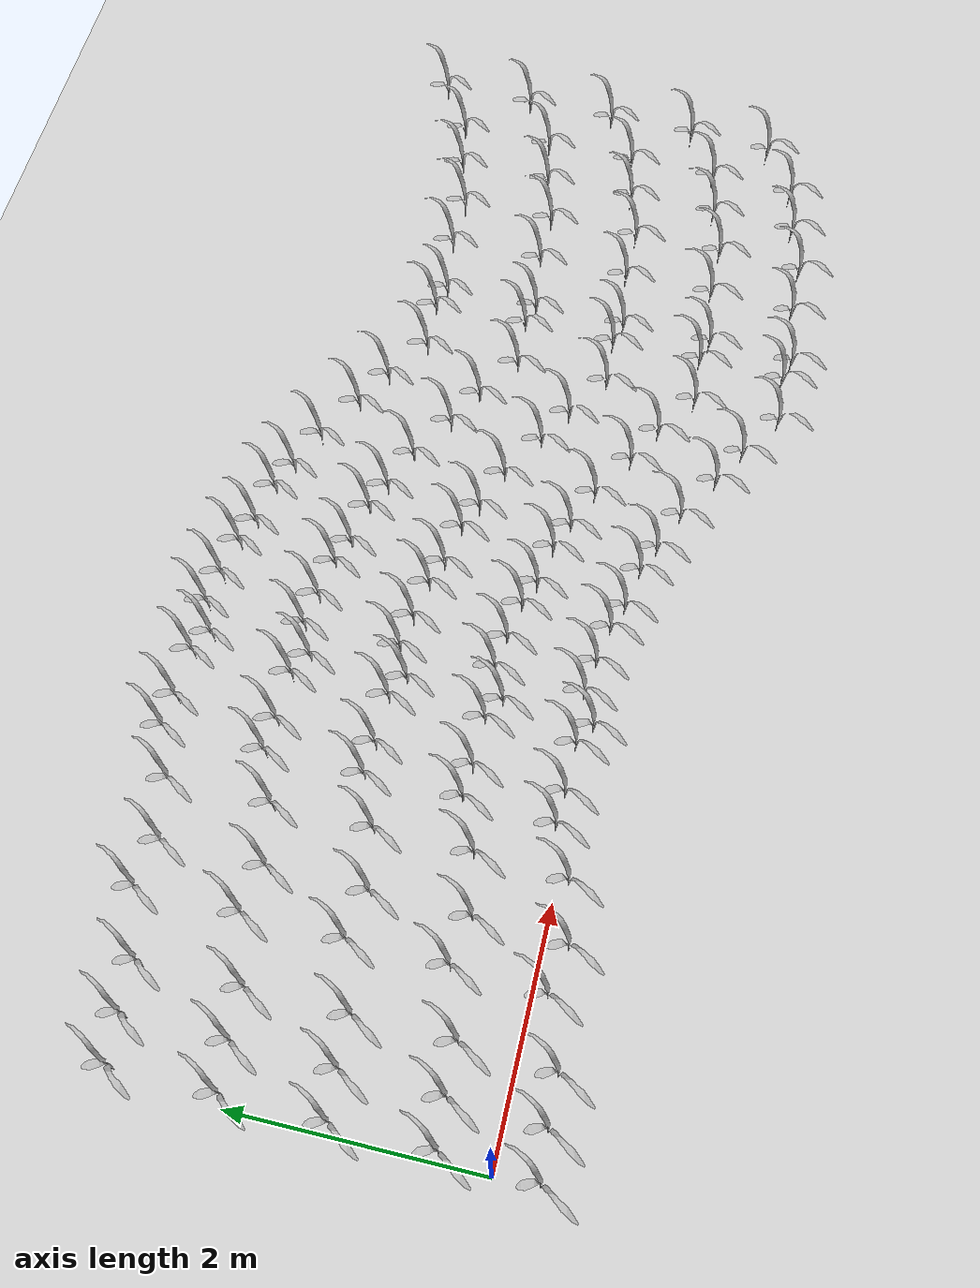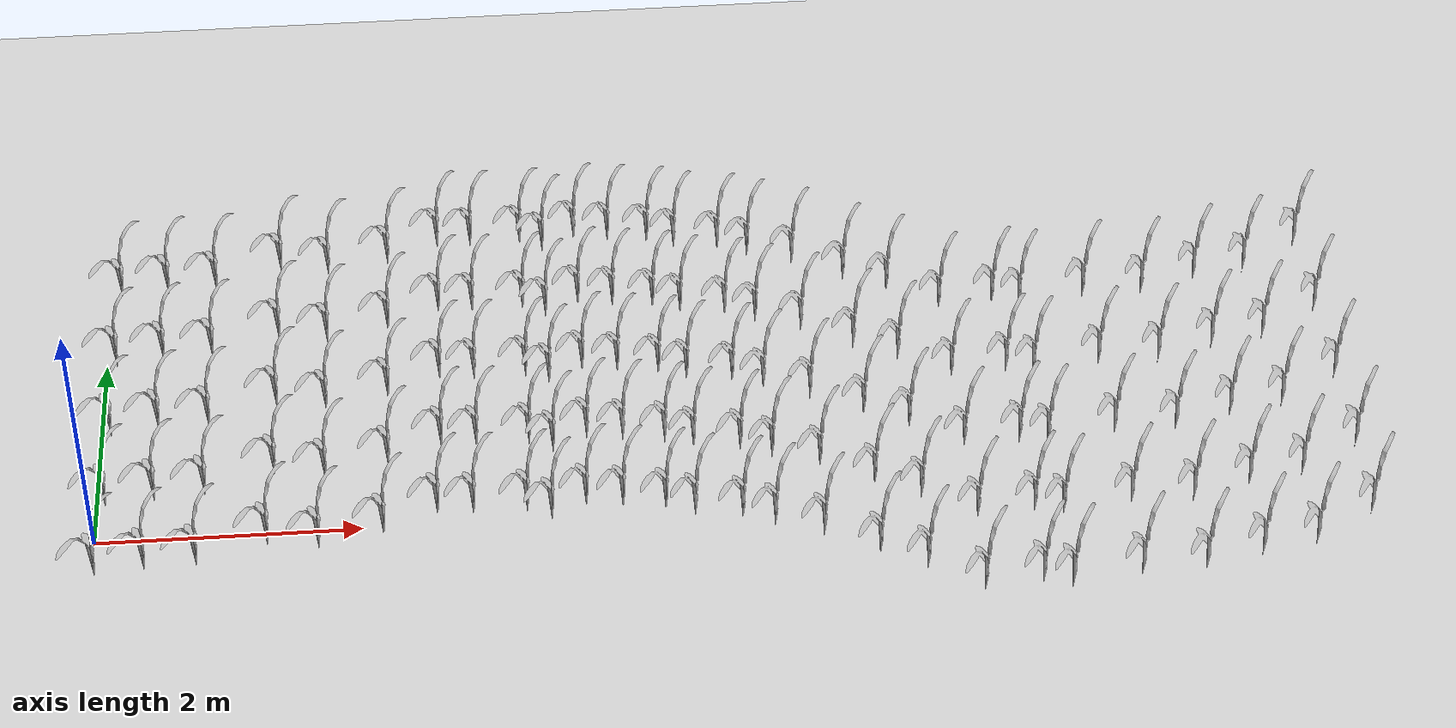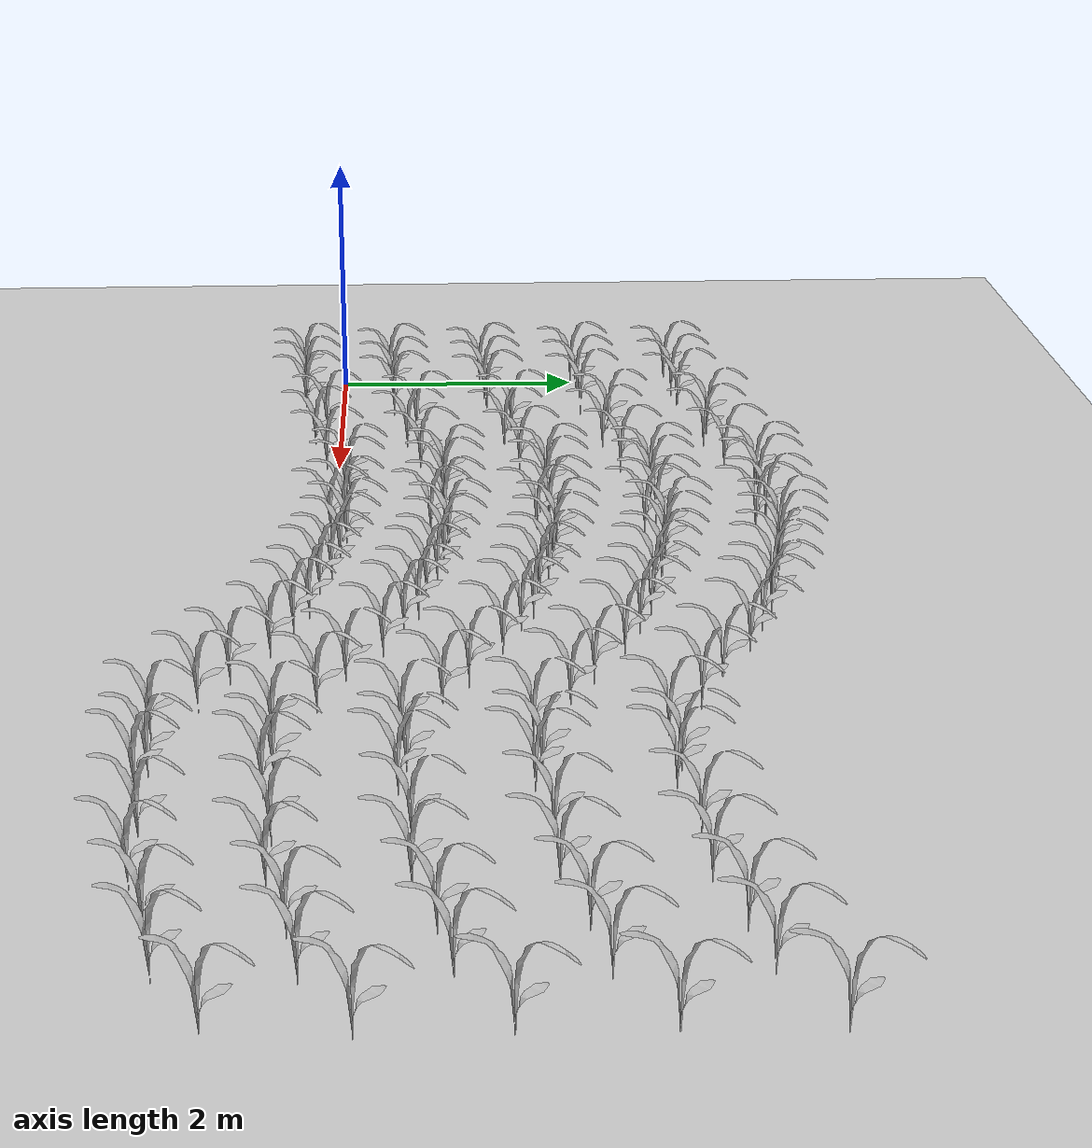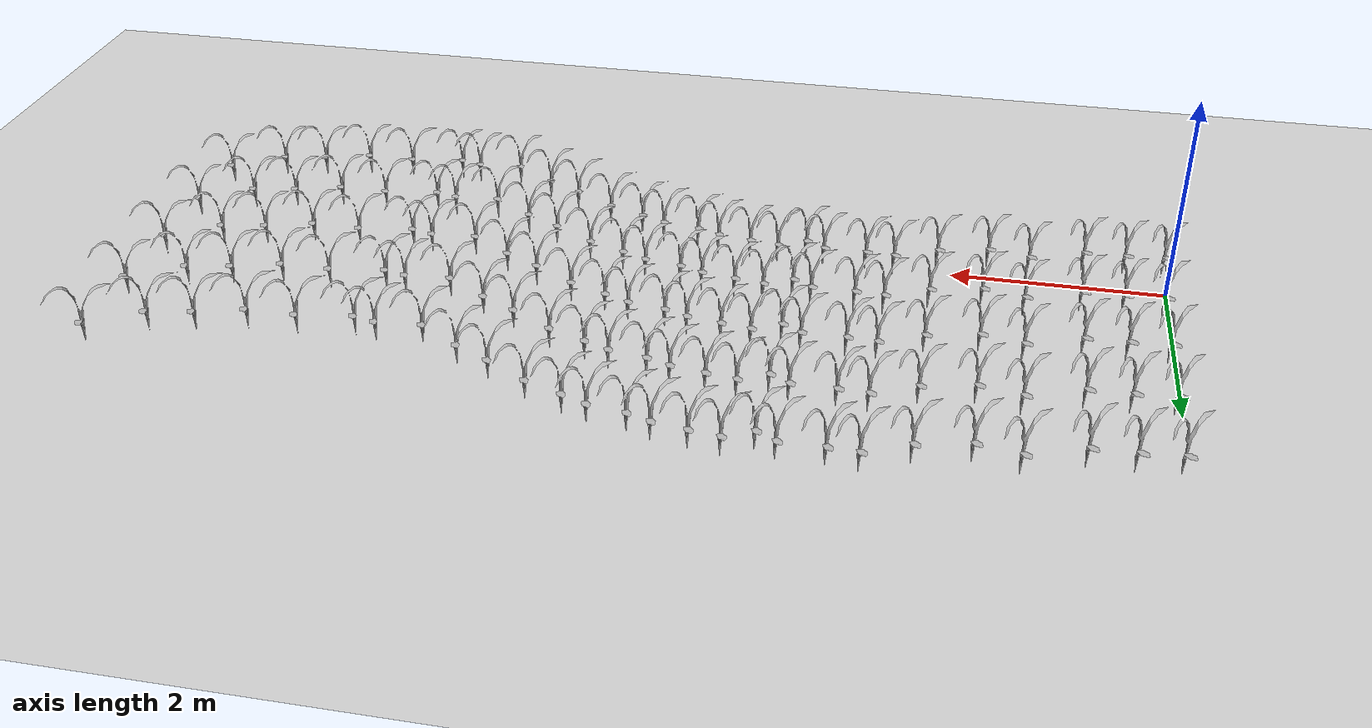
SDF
<sdf version="1.7">
 <world name="default">
  <scene><ambient>0.4 0.4 0.4 1</ambient><background>0.7 0.7 0.7 1</background><shadows>1</shadows></scene>
  <light name="sun" type="directional">
   <pose>0 0 10 0 -0 0</pose>
   <diffuse>0.8 0.8 0.8 1</diffuse>
   <specular>0.2 0.2 0.2 1</specular>
   <attenuation>
    <range>1000</range>
    <constant>0.9</constant>
    <linear>0.01</linear>
    <quadratic>0.001</quadratic>
   </attenuation>
   <direction>-0.5 0.1 -0.9</direction>
   <spot><inner_angle>0</inner_angle><outer_angle>0</outer_angle><falloff>0</falloff></spot>
  </light>
  <model name="ground_plane">
   <static>1</static>
   <link name="link">
    <collision name="collision">
     <geometry><plane><normal>0 0 1</normal><size>100 100</size></plane></geometry>
     <surface>
      <contact><collide_bitmask>65535</collide_bitmask></contact>
      <friction><ode><mu>100</mu><mu2>50</mu2></ode></friction>
     </surface>
    </collision>
    <visual name="visual">
     <cast_shadows>0</cast_shadows>
     <geometry><plane><normal>0 0 1</normal><size>100 100</size></plane></geometry>
     <material>
      <script><uri>file://media/materials/scripts/gazebo.material</uri><name>Gazebo/Grey</name></script>
     </material>
    </visual>
   </link>
  </model>
  <physics type="ode">
   <real_time_update_rate>1000</real_time_update_rate>
   <max_step_size>0.001</max_step_size>
   <real_time_factor>1</real_time_factor>
   <ode>
    <solver>
     <type>quick</type>
     <iters>150</iters>
     <precon_iters>0</precon_iters>
     <sor>1.4</sor>
     <use_dynamic_moi_rescaling>1</use_dynamic_moi_rescaling>
    </solver>
    <constraints>
     <cfm>1e-05</cfm>
     <erp>0.2</erp>
     <contact_max_correcting_vel>2000</contact_max_correcting_vel>
     <contact_surface_layer>0.01</contact_surface_layer>
    </constraints>
   </ode>
  </physics>
  <gravity>0 0 -9.8</gravity>
  <magnetic_field>6e-06 2.3e-05 -4.2e-05</magnetic_field>
  <atmosphere type="adiabatic"/>
  <spherical_coordinates>
   <surface_model>EARTH_WGS84</surface_model>
   <latitude_deg>0</latitude_deg>
   <longitude_deg>0</longitude_deg>
   <elevation>0</elevation>
   <heading_deg>0</heading_deg>
  </spherical_coordinates>
  <model name="maize_row">
   <model name="maize_02">
    <pose>-4.63661 0.027408 0 0 -0 0</pose>
    <link name="maize_02_link">
     <inertial>
      <pose>0 0 0.01 0 -0 0</pose>
      <mass>0.3</mass>
      <inertia>
       <ixx>0.00334167</ixx>
       <ixy>0</ixy>
       <ixz>0</ixz>
       <iyy>0.00334167</iyy>
       <iyz>0</iyz>
       <izz>1.66667e-05</izz>
      </inertia>
      <pose>0 0 0.1 0 -0 0</pose>
     </inertial>
     <collision name="collision">
      <pose>0 0 0.2 0 -0 0</pose>
      <geometry><box><size>0.02 0.02 0.4</size></box></geometry>
      <surface><friction><ode><mu>10</mu><mu2>10</mu2></ode></friction></surface>
     </collision>
     <visual name="visual">
      <geometry>
       <mesh><uri>model://maize_02/meshes/maize_02.dae</uri><scale>0.683166 0.683166 0.683166</scale></mesh>
      </geometry>
     </visual>
    </link>
   </model>
   <model name="maize_02_clone">
    <pose>-4.27241 0.05616 0 0 -0 0</pose>
    <link name="maize_02_link">
     <inertial>
      <pose>0 0 0.01 0 -0 0</pose>
      <mass>0.3</mass>
      <inertia>
       <ixx>0.00334167</ixx>
       <ixy>0</ixy>
       <ixz>0</ixz>
       <iyy>0.00334167</iyy>
       <iyz>0</iyz>
       <izz>1.66667e-05</izz>
      </inertia>
      <pose>0 0 0.1 0 -0 0</pose>
     </inertial>
     <collision name="collision">
      <pose>0 0 0.2 0 -0 0</pose>
      <geometry><box><size>0.02 0.02 0.4</size></box></geometry>
      <surface><friction><ode><mu>10</mu><mu2>10</mu2></ode></friction></surface>
     </collision>
     <visual name="visual">
      <geometry>
       <mesh><uri>model://maize_02/meshes/maize_02.dae</uri><scale>0.683166 0.683166 0.683166</scale></mesh>
      </geometry>
     </visual>
    </link>
   </model>
   <model name="maize_02_clone_0">
    <pose>-3.88904 0.065744 0 0 -0 0</pose>
    <link name="maize_02_link">
     <inertial>
      <pose>0 0 0.01 0 -0 0</pose>
      <mass>0.3</mass>
      <inertia>
       <ixx>0.00334167</ixx>
       <ixy>0</ixy>
       <ixz>0</ixz>
       <iyy>0.00334167</iyy>
       <iyz>0</iyz>
       <izz>1.66667e-05</izz>
      </inertia>
      <pose>0 0 0.1 0 -0 0</pose>
     </inertial>
     <collision name="collision">
      <pose>0 0 0.2 0 -0 0</pose>
      <geometry><box><size>0.02 0.02 0.4</size></box></geometry>
      <surface><friction><ode><mu>10</mu><mu2>10</mu2></ode></friction></surface>
     </collision>
     <visual name="visual">
      <geometry>
       <mesh><uri>model://maize_02/meshes/maize_02.dae</uri><scale>0.683166 0.683166 0.683166</scale></mesh>
      </geometry>
     </visual>
    </link>
   </model>
   <model name="maize_02_clone_1">
    <pose>-3.37149 0.257428 0 0 -0 0</pose>
    <link name="maize_02_link">
     <inertial>
      <pose>0 0 0.01 0 -0 0</pose>
      <mass>0.3</mass>
      <inertia>
       <ixx>0.00334167</ixx>
       <ixy>0</ixy>
       <ixz>0</ixz>
       <iyy>0.00334167</iyy>
       <iyz>0</iyz>
       <izz>1.66667e-05</izz>
      </inertia>
      <pose>0 0 0.1 0 -0 0</pose>
     </inertial>
     <collision name="collision">
      <pose>0 0 0.2 0 -0 0</pose>
      <geometry><box><size>0.02 0.02 0.4</size></box></geometry>
      <surface><friction><ode><mu>10</mu><mu2>10</mu2></ode></friction></surface>
     </collision>
     <visual name="visual">
      <geometry>
       <mesh><uri>model://maize_02/meshes/maize_02.dae</uri><scale>0.683166 0.683166 0.683166</scale></mesh>
      </geometry>
     </visual>
    </link>
   </model>
   <model name="maize_02_clone_10">
    <pose>-0.393317 0.390237 0 0 -0 0</pose>
    <link name="maize_02_link">
     <inertial>
      <pose>0 0 0.01 0 -0 0</pose>
      <mass>0.3</mass>
      <inertia>
       <ixx>0.00334167</ixx>
       <ixy>0</ixy>
       <ixz>0</ixz>
       <iyy>0.00334167</iyy>
       <iyz>0</iyz>
       <izz>1.66667e-05</izz>
      </inertia>
      <pose>0 0 0.1 0 -0 0</pose>
     </inertial>
     <collision name="collision">
      <pose>0 0 0.2 0 -0 0</pose>
      <geometry><box><size>0.02 0.02 0.4</size></box></geometry>
      <surface><friction><ode><mu>10</mu><mu2>10</mu2></ode></friction></surface>
     </collision>
     <visual name="visual">
      <geometry>
       <mesh><uri>model://maize_02/meshes/maize_02.dae</uri><scale>0.683166 0.683166 0.683166</scale></mesh>
      </geometry>
     </visual>
    </link>
   </model>
   <model name="maize_02_clone_11">
    <pose>0.410873 0.154867 0 0 -0 0</pose>
    <link name="maize_02_link">
     <inertial>
      <pose>0 0 0.01 0 -0 0</pose>
      <mass>0.3</mass>
      <inertia>
       <ixx>0.00334167</ixx>
       <ixy>0</ixy>
       <ixz>0</ixz>
       <iyy>0.00334167</iyy>
       <iyz>0</iyz>
       <izz>1.66667e-05</izz>
      </inertia>
      <pose>0 0 0.1 0 -0 0</pose>
     </inertial>
     <collision name="collision">
      <pose>0 0 0.2 0 -0 0</pose>
      <geometry><box><size>0.02 0.02 0.4</size></box></geometry>
      <surface><friction><ode><mu>10</mu><mu2>10</mu2></ode></friction></surface>
     </collision>
     <visual name="visual">
      <geometry>
       <mesh><uri>model://maize_02/meshes/maize_02.dae</uri><scale>0.683166 0.683166 0.683166</scale></mesh>
      </geometry>
     </visual>
    </link>
   </model>
   <model name="maize_02_clone_12">
    <pose>0.175502 0.252945 0 0 -0 0</pose>
    <link name="maize_02_link">
     <inertial>
      <pose>0 0 0.01 0 -0 0</pose>
      <mass>0.3</mass>
      <inertia>
       <ixx>0.00334167</ixx>
       <ixy>0</ixy>
       <ixz>0</ixz>
       <iyy>0.00334167</iyy>
       <iyz>0</iyz>
       <izz>1.66667e-05</izz>
      </inertia>
      <pose>0 0 0.1 0 -0 0</pose>
     </inertial>
     <collision name="collision">
      <pose>0 0 0.2 0 -0 0</pose>
      <geometry><box><size>0.02 0.02 0.4</size></box></geometry>
      <surface><friction><ode><mu>10</mu><mu2>10</mu2></ode></friction></surface>
     </collision>
     <visual name="visual">
      <geometry>
       <mesh><uri>model://maize_02/meshes/maize_02.dae</uri><scale>0.683166 0.683166 0.683166</scale></mesh>
      </geometry>
     </visual>
    </link>
   </model>
   <model name="maize_02_clone_13">
    <pose>0.76395 0.017569 0 0 -0 0</pose>
    <link name="maize_02_link">
     <inertial>
      <pose>0 0 0.01 0 -0 0</pose>
      <mass>0.3</mass>
      <inertia>
       <ixx>0.00334167</ixx>
       <ixy>0</ixy>
       <ixz>0</ixz>
       <iyy>0.00334167</iyy>
       <iyz>0</iyz>
       <izz>1.66667e-05</izz>
      </inertia>
      <pose>0 0 0.1 0 -0 0</pose>
     </inertial>
     <collision name="collision">
      <pose>0 0 0.2 0 -0 0</pose>
      <geometry><box><size>0.02 0.02 0.4</size></box></geometry>
      <surface><friction><ode><mu>10</mu><mu2>10</mu2></ode></friction></surface>
     </collision>
     <visual name="visual">
      <geometry>
       <mesh><uri>model://maize_02/meshes/maize_02.dae</uri><scale>0.683166 0.683166 0.683166</scale></mesh>
      </geometry>
     </visual>
    </link>
   </model>
   <model name="maize_02_clone_14">
    <pose>1.15624 -0.217806 0 0 -0 0</pose>
    <link name="maize_02_link">
     <inertial>
      <pose>0 0 0.01 0 -0 0</pose>
      <mass>0.3</mass>
      <inertia>
       <ixx>0.00334167</ixx>
       <ixy>0</ixy>
       <ixz>0</ixz>
       <iyy>0.00334167</iyy>
       <iyz>0</iyz>
       <izz>1.66667e-05</izz>
      </inertia>
      <pose>0 0 0.1 0 -0 0</pose>
     </inertial>
     <collision name="collision">
      <pose>0 0 0.2 0 -0 0</pose>
      <geometry><box><size>0.02 0.02 0.4</size></box></geometry>
      <surface><friction><ode><mu>10</mu><mu2>10</mu2></ode></friction></surface>
     </collision>
     <visual name="visual">
      <geometry>
       <mesh><uri>model://maize_02/meshes/maize_02.dae</uri><scale>0.683166 0.683166 0.683166</scale></mesh>
      </geometry>
     </visual>
    </link>
   </model>
   <model name="maize_02_clone_15">
    <pose>1.48967 -0.39434 0 0 -0 0</pose>
    <link name="maize_02_link">
     <inertial>
      <pose>0 0 0.01 0 -0 0</pose>
      <mass>0.3</mass>
      <inertia>
       <ixx>0.00334167</ixx>
       <ixy>0</ixy>
       <ixz>0</ixz>
       <iyy>0.00334167</iyy>
       <iyz>0</iyz>
       <izz>1.66667e-05</izz>
      </inertia>
      <pose>0 0 0.1 0 -0 0</pose>
     </inertial>
     <collision name="collision">
      <pose>0 0 0.2 0 -0 0</pose>
      <geometry><box><size>0.02 0.02 0.4</size></box></geometry>
      <surface><friction><ode><mu>10</mu><mu2>10</mu2></ode></friction></surface>
     </collision>
     <visual name="visual">
      <geometry>
       <mesh><uri>model://maize_02/meshes/maize_02.dae</uri><scale>0.683166 0.683166 0.683166</scale></mesh>
      </geometry>
     </visual>
    </link>
   </model>
   <model name="maize_02_clone_16">
    <pose>1.88196 -0.649333 0 0 -0 0</pose>
    <link name="maize_02_link">
     <inertial>
      <pose>0 0 0.01 0 -0 0</pose>
      <mass>0.3</mass>
      <inertia>
       <ixx>0.00334167</ixx>
       <ixy>0</ixy>
       <ixz>0</ixz>
       <iyy>0.00334167</iyy>
       <iyz>0</iyz>
       <izz>1.66667e-05</izz>
      </inertia>
      <pose>0 0 0.1 0 -0 0</pose>
     </inertial>
     <collision name="collision">
      <pose>0 0 0.2 0 -0 0</pose>
      <geometry><box><size>0.02 0.02 0.4</size></box></geometry>
      <surface><friction><ode><mu>10</mu><mu2>10</mu2></ode></friction></surface>
     </collision>
     <visual name="visual">
      <geometry>
       <mesh><uri>model://maize_02/meshes/maize_02.dae</uri><scale>0.683166 0.683166 0.683166</scale></mesh>
      </geometry>
     </visual>
    </link>
   </model>
   <model name="maize_02_clone_17">
    <pose>2.52627 -0.672048 0 0 -0 0</pose>
    <link name="maize_02_link">
     <inertial>
      <pose>0 0 0.01 0 -0 0</pose>
      <mass>0.3</mass>
      <inertia>
       <ixx>0.00334167</ixx>
       <ixy>0</ixy>
       <ixz>0</ixz>
       <iyy>0.00334167</iyy>
       <iyz>0</iyz>
       <izz>1.66667e-05</izz>
      </inertia>
      <pose>0 0 0.1 0 -0 0</pose>
     </inertial>
     <collision name="collision">
      <pose>0 0 0.2 0 -0 0</pose>
      <geometry><box><size>0.02 0.02 0.4</size></box></geometry>
      <surface><friction><ode><mu>10</mu><mu2>10</mu2></ode></friction></surface>
     </collision>
     <visual name="visual">
      <geometry>
       <mesh><uri>model://maize_02/meshes/maize_02.dae</uri><scale>0.683166 0.683166 0.683166</scale></mesh>
      </geometry>
     </visual>
    </link>
   </model>
   <model name="maize_02_clone_18">
    <pose>2.3152 -0.619273 0 0 -0 0</pose>
    <link name="maize_02_link">
     <inertial>
      <pose>0 0 0.01 0 -0 0</pose>
      <mass>0.3</mass>
      <inertia>
       <ixx>0.00334167</ixx>
       <ixy>0</ixy>
       <ixz>0</ixz>
       <iyy>0.00334167</iyy>
       <iyz>0</iyz>
       <izz>1.66667e-05</izz>
      </inertia>
      <pose>0 0 0.1 0 -0 0</pose>
     </inertial>
     <collision name="collision">
      <pose>0 0 0.2 0 -0 0</pose>
      <geometry><box><size>0.02 0.02 0.4</size></box></geometry>
      <surface><friction><ode><mu>10</mu><mu2>10</mu2></ode></friction></surface>
     </collision>
     <visual name="visual">
      <geometry>
       <mesh><uri>model://maize_02/meshes/maize_02.dae</uri><scale>0.683166 0.683166 0.683166</scale></mesh>
      </geometry>
     </visual>
    </link>
   </model>
   <model name="maize_02_clone_19">
    <pose>3.05425 -0.592874 0 0 -0 0</pose>
    <link name="maize_02_link">
     <inertial>
      <pose>0 0 0.01 0 -0 0</pose>
      <mass>0.3</mass>
      <inertia>
       <ixx>0.00334167</ixx>
       <ixy>0</ixy>
       <ixz>0</ixz>
       <iyy>0.00334167</iyy>
       <iyz>0</iyz>
       <izz>1.66667e-05</izz>
      </inertia>
      <pose>0 0 0.1 0 -0 0</pose>
     </inertial>
     <collision name="collision">
      <pose>0 0 0.2 0 -0 0</pose>
      <geometry><box><size>0.02 0.02 0.4</size></box></geometry>
      <surface><friction><ode><mu>10</mu><mu2>10</mu2></ode></friction></surface>
     </collision>
     <visual name="visual">
      <geometry>
       <mesh><uri>model://maize_02/meshes/maize_02.dae</uri><scale>0.683166 0.683166 0.683166</scale></mesh>
      </geometry>
     </visual>
    </link>
   </model>
   <model name="maize_02_clone_2">
    <pose>-2.98813 0.180754 0 0 -0 0</pose>
    <link name="maize_02_link">
     <inertial>
      <pose>0 0 0.01 0 -0 0</pose>
      <mass>0.3</mass>
      <inertia>
       <ixx>0.00334167</ixx>
       <ixy>0</ixy>
       <ixz>0</ixz>
       <iyy>0.00334167</iyy>
       <iyz>0</iyz>
       <izz>1.66667e-05</izz>
      </inertia>
      <pose>0 0 0.1 0 -0 0</pose>
     </inertial>
     <collision name="collision">
      <pose>0 0 0.2 0 -0 0</pose>
      <geometry><box><size>0.02 0.02 0.4</size></box></geometry>
      <surface><friction><ode><mu>10</mu><mu2>10</mu2></ode></friction></surface>
     </collision>
     <visual name="visual">
      <geometry>
       <mesh><uri>model://maize_02/meshes/maize_02.dae</uri><scale>0.683166 0.683166 0.683166</scale></mesh>
      </geometry>
     </visual>
    </link>
   </model>
   <model name="maize_02_clone_20">
    <pose>3.5294 -0.592874 0 0 -0 0</pose>
    <link name="maize_02_link">
     <inertial>
      <pose>0 0 0.01 0 -0 0</pose>
      <mass>0.3</mass>
      <inertia>
       <ixx>0.00334167</ixx>
       <ixy>0</ixy>
       <ixz>0</ixz>
       <iyy>0.00334167</iyy>
       <iyz>0</iyz>
       <izz>1.66667e-05</izz>
      </inertia>
      <pose>0 0 0.1 0 -0 0</pose>
     </inertial>
     <collision name="collision">
      <pose>0 0 0.2 0 -0 0</pose>
      <geometry><box><size>0.02 0.02 0.4</size></box></geometry>
      <surface><friction><ode><mu>10</mu><mu2>10</mu2></ode></friction></surface>
     </collision>
     <visual name="visual">
      <geometry>
       <mesh><uri>model://maize_02/meshes/maize_02.dae</uri><scale>0.683166 0.683166 0.683166</scale></mesh>
      </geometry>
     </visual>
    </link>
   </model>
   <model name="maize_02_clone_21">
    <pose>3.97801 -0.460902 0 0 -0 0</pose>
    <link name="maize_02_link">
     <inertial>
      <pose>0 0 0.01 0 -0 0</pose>
      <mass>0.3</mass>
      <inertia>
       <ixx>0.00334167</ixx>
       <ixy>0</ixy>
       <ixz>0</ixz>
       <iyy>0.00334167</iyy>
       <iyz>0</iyz>
       <izz>1.66667e-05</izz>
      </inertia>
      <pose>0 0 0.1 0 -0 0</pose>
     </inertial>
     <collision name="collision">
      <pose>0 0 0.2 0 -0 0</pose>
      <geometry><box><size>0.02 0.02 0.4</size></box></geometry>
      <surface><friction><ode><mu>10</mu><mu2>10</mu2></ode></friction></surface>
     </collision>
     <visual name="visual">
      <geometry>
       <mesh><uri>model://maize_02/meshes/maize_02.dae</uri><scale>0.683166 0.683166 0.683166</scale></mesh>
      </geometry>
     </visual>
    </link>
   </model>
   <model name="maize_02_clone_22">
    <pose>4.40033 -0.381713 0 0 -0 0</pose>
    <link name="maize_02_link">
     <inertial>
      <pose>0 0 0.01 0 -0 0</pose>
      <mass>0.3</mass>
      <inertia>
       <ixx>0.00334167</ixx>
       <ixy>0</ixy>
       <ixz>0</ixz>
       <iyy>0.00334167</iyy>
       <iyz>0</iyz>
       <izz>1.66667e-05</izz>
      </inertia>
      <pose>0 0 0.1 0 -0 0</pose>
     </inertial>
     <collision name="collision">
      <pose>0 0 0.2 0 -0 0</pose>
      <geometry><box><size>0.02 0.02 0.4</size></box></geometry>
      <surface><friction><ode><mu>10</mu><mu2>10</mu2></ode></friction></surface>
     </collision>
     <visual name="visual">
      <geometry>
       <mesh><uri>model://maize_02/meshes/maize_02.dae</uri><scale>0.683166 0.683166 0.683166</scale></mesh>
      </geometry>
     </visual>
    </link>
   </model>
   <model name="maize_02_clone_23">
    <pose>4.87542 -0.091378 0 0 -0 0</pose>
    <link name="maize_02_link">
     <inertial>
      <pose>0 0 0.01 0 -0 0</pose>
      <mass>0.3</mass>
      <inertia>
       <ixx>0.00334167</ixx>
       <ixy>0</ixy>
       <ixz>0</ixz>
       <iyy>0.00334167</iyy>
       <iyz>0</iyz>
       <izz>1.66667e-05</izz>
      </inertia>
      <pose>0 0 0.1 0 -0 0</pose>
     </inertial>
     <collision name="collision">
      <pose>0 0 0.2 0 -0 0</pose>
      <geometry><box><size>0.02 0.02 0.4</size></box></geometry>
      <surface><friction><ode><mu>10</mu><mu2>10</mu2></ode></friction></surface>
     </collision>
     <visual name="visual">
      <geometry>
       <mesh><uri>model://maize_02/meshes/maize_02.dae</uri><scale>0.683166 0.683166 0.683166</scale></mesh>
      </geometry>
     </visual>
    </link>
   </model>
   <model name="maize_02_clone_24">
    <pose>-0.987177 0.483854 0 0 -0 0</pose>
    <link name="maize_02_link">
     <inertial>
      <pose>0 0 0.01 0 -0 0</pose>
      <mass>0.3</mass>
      <inertia>
       <ixx>0.00334167</ixx>
       <ixy>0</ixy>
       <ixz>0</ixz>
       <iyy>0.00334167</iyy>
       <iyz>0</iyz>
       <izz>1.66667e-05</izz>
      </inertia>
      <pose>0 0 0.1 0 -0 0</pose>
     </inertial>
     <collision name="collision">
      <pose>0 0 0.2 0 -0 0</pose>
      <geometry><box><size>0.02 0.02 0.4</size></box></geometry>
      <surface><friction><ode><mu>10</mu><mu2>10</mu2></ode></friction></surface>
     </collision>
     <visual name="visual">
      <geometry>
       <mesh><uri>model://maize_02/meshes/maize_02.dae</uri><scale>0.683166 0.683166 0.683166</scale></mesh>
      </geometry>
     </visual>
    </link>
   </model>
   <model name="maize_02_clone_3">
    <pose>-2.50892 0.28618 0 0 -0 0</pose>
    <link name="maize_02_link">
     <inertial>
      <pose>0 0 0.01 0 -0 0</pose>
      <mass>0.3</mass>
      <inertia>
       <ixx>0.00334167</ixx>
       <ixy>0</ixy>
       <ixz>0</ixz>
       <iyy>0.00334167</iyy>
       <iyz>0</iyz>
       <izz>1.66667e-05</izz>
      </inertia>
      <pose>0 0 0.1 0 -0 0</pose>
     </inertial>
     <collision name="collision">
      <pose>0 0 0.2 0 -0 0</pose>
      <geometry><box><size>0.02 0.02 0.4</size></box></geometry>
      <surface><friction><ode><mu>10</mu><mu2>10</mu2></ode></friction></surface>
     </collision>
     <visual name="visual">
      <geometry>
       <mesh><uri>model://maize_02/meshes/maize_02.dae</uri><scale>0.683166 0.683166 0.683166</scale></mesh>
      </geometry>
     </visual>
    </link>
   </model>
   <model name="maize_02_clone_4">
    <pose>-1.83451 0.458469 0 0 -0 0</pose>
    <link name="maize_02_link">
     <inertial>
      <pose>0 0 0.01 0 -0 0</pose>
      <mass>0.3</mass>
      <inertia>
       <ixx>0.00334167</ixx>
       <ixy>0</ixy>
       <ixz>0</ixz>
       <iyy>0.00334167</iyy>
       <iyz>0</iyz>
       <izz>1.66667e-05</izz>
      </inertia>
      <pose>0 0 0.1 0 -0 0</pose>
     </inertial>
     <collision name="collision">
      <pose>0 0 0.2 0 -0 0</pose>
      <geometry><box><size>0.02 0.02 0.4</size></box></geometry>
      <surface><friction><ode><mu>10</mu><mu2>10</mu2></ode></friction></surface>
     </collision>
     <visual name="visual">
      <geometry>
       <mesh><uri>model://maize_02/meshes/maize_02.dae</uri><scale>0.683166 0.683166 0.683166</scale></mesh>
      </geometry>
     </visual>
    </link>
   </model>
   <model name="maize_02_clone_5">
    <pose>-1.25106 0.353746 0 0 -0 0</pose>
    <link name="maize_02_link">
     <inertial>
      <pose>0 0 0.01 0 -0 0</pose>
      <mass>0.3</mass>
      <inertia>
       <ixx>0.00334167</ixx>
       <ixy>0</ixy>
       <ixz>0</ixz>
       <iyy>0.00334167</iyy>
       <iyz>0</iyz>
       <izz>1.66667e-05</izz>
      </inertia>
      <pose>0 0 0.1 0 -0 0</pose>
     </inertial>
     <collision name="collision">
      <pose>0 0 0.2 0 -0 0</pose>
      <geometry><box><size>0.02 0.02 0.4</size></box></geometry>
      <surface><friction><ode><mu>10</mu><mu2>10</mu2></ode></friction></surface>
     </collision>
     <visual name="visual">
      <geometry>
       <mesh><uri>model://maize_02/meshes/maize_02.dae</uri><scale>0.683166 0.683166 0.683166</scale></mesh>
      </geometry>
     </visual>
    </link>
   </model>
   <model name="maize_02_clone_6">
    <pose>-1.43059 0.458469 0 0 -0 0</pose>
    <link name="maize_02_link">
     <inertial>
      <pose>0 0 0.01 0 -0 0</pose>
      <mass>0.3</mass>
      <inertia>
       <ixx>0.00334167</ixx>
       <ixy>0</ixy>
       <ixz>0</ixz>
       <iyy>0.00334167</iyy>
       <iyz>0</iyz>
       <izz>1.66667e-05</izz>
      </inertia>
      <pose>0 0 0.1 0 -0 0</pose>
     </inertial>
     <collision name="collision">
      <pose>0 0 0.2 0 -0 0</pose>
      <geometry><box><size>0.02 0.02 0.4</size></box></geometry>
      <surface><friction><ode><mu>10</mu><mu2>10</mu2></ode></friction></surface>
     </collision>
     <visual name="visual">
      <geometry>
       <mesh><uri>model://maize_02/meshes/maize_02.dae</uri><scale>0.683166 0.683166 0.683166</scale></mesh>
      </geometry>
     </visual>
    </link>
   </model>
   <model name="maize_02_clone_7">
    <pose>-2.10378 0.473427 0 0 -0 0</pose>
    <link name="maize_02_link">
     <inertial>
      <pose>0 0 0.01 0 -0 0</pose>
      <mass>0.3</mass>
      <inertia>
       <ixx>0.00334167</ixx>
       <ixy>0</ixy>
       <ixz>0</ixz>
       <iyy>0.00334167</iyy>
       <iyz>0</iyz>
       <izz>1.66667e-05</izz>
      </inertia>
      <pose>0 0 0.1 0 -0 0</pose>
     </inertial>
     <collision name="collision">
      <pose>0 0 0.2 0 -0 0</pose>
      <geometry><box><size>0.02 0.02 0.4</size></box></geometry>
      <surface><friction><ode><mu>10</mu><mu2>10</mu2></ode></friction></surface>
     </collision>
     <visual name="visual">
      <geometry>
       <mesh><uri>model://maize_02/meshes/maize_02.dae</uri><scale>0.683166 0.683166 0.683166</scale></mesh>
      </geometry>
     </visual>
    </link>
   </model>
   <model name="maize_02_clone_8">
    <pose>-0.712516 0.443508 0 0 -0 0</pose>
    <link name="maize_02_link">
     <inertial>
      <pose>0 0 0.01 0 -0 0</pose>
      <mass>0.3</mass>
      <inertia>
       <ixx>0.00334167</ixx>
       <ixy>0</ixy>
       <ixz>0</ixz>
       <iyy>0.00334167</iyy>
       <iyz>0</iyz>
       <izz>1.66667e-05</izz>
      </inertia>
      <pose>0 0 0.1 0 -0 0</pose>
     </inertial>
     <collision name="collision">
      <pose>0 0 0.2 0 -0 0</pose>
      <geometry><box><size>0.02 0.02 0.4</size></box></geometry>
      <surface><friction><ode><mu>10</mu><mu2>10</mu2></ode></friction></surface>
     </collision>
     <visual name="visual">
      <geometry>
       <mesh><uri>model://maize_02/meshes/maize_02.dae</uri><scale>0.683166 0.683166 0.683166</scale></mesh>
      </geometry>
     </visual>
    </link>
   </model>
   <model name="maize_02_clone_9">
    <pose>-0.177553 0.311777 0 0 -0 0</pose>
    <link name="maize_02_link">
     <inertial>
      <pose>0 0 0.01 0 -0 0</pose>
      <mass>0.3</mass>
      <inertia>
       <ixx>0.00334167</ixx>
       <ixy>0</ixy>
       <ixz>0</ixz>
       <iyy>0.00334167</iyy>
       <iyz>0</iyz>
       <izz>1.66667e-05</izz>
      </inertia>
      <pose>0 0 0.1 0 -0 0</pose>
     </inertial>
     <collision name="collision">
      <pose>0 0 0.2 0 -0 0</pose>
      <geometry><box><size>0.02 0.02 0.4</size></box></geometry>
      <surface><friction><ode><mu>10</mu><mu2>10</mu2></ode></friction></surface>
     </collision>
     <visual name="visual">
      <geometry>
       <mesh><uri>model://maize_02/meshes/maize_02.dae</uri><scale>0.683166 0.683166 0.683166</scale></mesh>
      </geometry>
     </visual>
    </link>
   </model>
   <static>0</static>
   <pose>4.70004 0.375 2e-05 0 -4e-06 0</pose>
  </model>
  <model name="maize_row_clone">
   <model name="maize_02">
    <pose>-4.63661 0.027408 0 0 -0 0</pose>
    <link name="maize_02_link">
     <inertial>
      <pose>0 0 0.01 0 -0 0</pose>
      <mass>0.3</mass>
      <inertia>
       <ixx>0.00334167</ixx>
       <ixy>0</ixy>
       <ixz>0</ixz>
       <iyy>0.00334167</iyy>
       <iyz>0</iyz>
       <izz>1.66667e-05</izz>
      </inertia>
      <pose>0 0 0.1 0 -0 0</pose>
     </inertial>
     <collision name="collision">
      <pose>0 0 0.2 0 -0 0</pose>
      <geometry><box><size>0.02 0.02 0.4</size></box></geometry>
      <surface><friction><ode><mu>10</mu><mu2>10</mu2></ode></friction></surface>
     </collision>
     <visual name="visual">
      <geometry>
       <mesh><uri>model://maize_02/meshes/maize_02.dae</uri><scale>0.683166 0.683166 0.683166</scale></mesh>
      </geometry>
     </visual>
    </link>
   </model>
   <model name="maize_02_clone">
    <pose>-4.27241 0.05616 0 0 -0 0</pose>
    <link name="maize_02_link">
     <inertial>
      <pose>0 0 0.01 0 -0 0</pose>
      <mass>0.3</mass>
      <inertia>
       <ixx>0.00334167</ixx>
       <ixy>0</ixy>
       <ixz>0</ixz>
       <iyy>0.00334167</iyy>
       <iyz>0</iyz>
       <izz>1.66667e-05</izz>
      </inertia>
      <pose>0 0 0.1 0 -0 0</pose>
     </inertial>
     <collision name="collision">
      <pose>0 0 0.2 0 -0 0</pose>
      <geometry><box><size>0.02 0.02 0.4</size></box></geometry>
      <surface><friction><ode><mu>10</mu><mu2>10</mu2></ode></friction></surface>
     </collision>
     <visual name="visual">
      <geometry>
       <mesh><uri>model://maize_02/meshes/maize_02.dae</uri><scale>0.683166 0.683166 0.683166</scale></mesh>
      </geometry>
     </visual>
    </link>
   </model>
   <model name="maize_02_clone_0">
    <pose>-3.88904 0.065744 0 0 -0 0</pose>
    <link name="maize_02_link">
     <inertial>
      <pose>0 0 0.01 0 -0 0</pose>
      <mass>0.3</mass>
      <inertia>
       <ixx>0.00334167</ixx>
       <ixy>0</ixy>
       <ixz>0</ixz>
       <iyy>0.00334167</iyy>
       <iyz>0</iyz>
       <izz>1.66667e-05</izz>
      </inertia>
      <pose>0 0 0.1 0 -0 0</pose>
     </inertial>
     <collision name="collision">
      <pose>0 0 0.2 0 -0 0</pose>
      <geometry><box><size>0.02 0.02 0.4</size></box></geometry>
      <surface><friction><ode><mu>10</mu><mu2>10</mu2></ode></friction></surface>
     </collision>
     <visual name="visual">
      <geometry>
       <mesh><uri>model://maize_02/meshes/maize_02.dae</uri><scale>0.683166 0.683166 0.683166</scale></mesh>
      </geometry>
     </visual>
    </link>
   </model>
   <model name="maize_02_clone_1">
    <pose>-3.37149 0.257428 0 0 -0 0</pose>
    <link name="maize_02_link">
     <inertial>
      <pose>0 0 0.01 0 -0 0</pose>
      <mass>0.3</mass>
      <inertia>
       <ixx>0.00334167</ixx>
       <ixy>0</ixy>
       <ixz>0</ixz>
       <iyy>0.00334167</iyy>
       <iyz>0</iyz>
       <izz>1.66667e-05</izz>
      </inertia>
      <pose>0 0 0.1 0 -0 0</pose>
     </inertial>
     <collision name="collision">
      <pose>0 0 0.2 0 -0 0</pose>
      <geometry><box><size>0.02 0.02 0.4</size></box></geometry>
      <surface><friction><ode><mu>10</mu><mu2>10</mu2></ode></friction></surface>
     </collision>
     <visual name="visual">
      <geometry>
       <mesh><uri>model://maize_02/meshes/maize_02.dae</uri><scale>0.683166 0.683166 0.683166</scale></mesh>
      </geometry>
     </visual>
    </link>
   </model>
   <model name="maize_02_clone_10">
    <pose>-0.393317 0.390237 0 0 -0 0</pose>
    <link name="maize_02_link">
     <inertial>
      <pose>0 0 0.01 0 -0 0</pose>
      <mass>0.3</mass>
      <inertia>
       <ixx>0.00334167</ixx>
       <ixy>0</ixy>
       <ixz>0</ixz>
       <iyy>0.00334167</iyy>
       <iyz>0</iyz>
       <izz>1.66667e-05</izz>
      </inertia>
      <pose>0 0 0.1 0 -0 0</pose>
     </inertial>
     <collision name="collision">
      <pose>0 0 0.2 0 -0 0</pose>
      <geometry><box><size>0.02 0.02 0.4</size></box></geometry>
      <surface><friction><ode><mu>10</mu><mu2>10</mu2></ode></friction></surface>
     </collision>
     <visual name="visual">
      <geometry>
       <mesh><uri>model://maize_02/meshes/maize_02.dae</uri><scale>0.683166 0.683166 0.683166</scale></mesh>
      </geometry>
     </visual>
    </link>
   </model>
   <model name="maize_02_clone_11">
    <pose>0.410873 0.154867 0 0 -0 0</pose>
    <link name="maize_02_link">
     <inertial>
      <pose>0 0 0.01 0 -0 0</pose>
      <mass>0.3</mass>
      <inertia>
       <ixx>0.00334167</ixx>
       <ixy>0</ixy>
       <ixz>0</ixz>
       <iyy>0.00334167</iyy>
       <iyz>0</iyz>
       <izz>1.66667e-05</izz>
      </inertia>
      <pose>0 0 0.1 0 -0 0</pose>
     </inertial>
     <collision name="collision">
      <pose>0 0 0.2 0 -0 0</pose>
      <geometry><box><size>0.02 0.02 0.4</size></box></geometry>
      <surface><friction><ode><mu>10</mu><mu2>10</mu2></ode></friction></surface>
     </collision>
     <visual name="visual">
      <geometry>
       <mesh><uri>model://maize_02/meshes/maize_02.dae</uri><scale>0.683166 0.683166 0.683166</scale></mesh>
      </geometry>
     </visual>
    </link>
   </model>
   <model name="maize_02_clone_12">
    <pose>0.175502 0.252945 0 0 -0 0</pose>
    <link name="maize_02_link">
     <inertial>
      <pose>0 0 0.01 0 -0 0</pose>
      <mass>0.3</mass>
      <inertia>
       <ixx>0.00334167</ixx>
       <ixy>0</ixy>
       <ixz>0</ixz>
       <iyy>0.00334167</iyy>
       <iyz>0</iyz>
       <izz>1.66667e-05</izz>
      </inertia>
      <pose>0 0 0.1 0 -0 0</pose>
     </inertial>
     <collision name="collision">
      <pose>0 0 0.2 0 -0 0</pose>
      <geometry><box><size>0.02 0.02 0.4</size></box></geometry>
      <surface><friction><ode><mu>10</mu><mu2>10</mu2></ode></friction></surface>
     </collision>
     <visual name="visual">
      <geometry>
       <mesh><uri>model://maize_02/meshes/maize_02.dae</uri><scale>0.683166 0.683166 0.683166</scale></mesh>
      </geometry>
     </visual>
    </link>
   </model>
   <model name="maize_02_clone_13">
    <pose>0.76395 0.017569 0 0 -0 0</pose>
    <link name="maize_02_link">
     <inertial>
      <pose>0 0 0.01 0 -0 0</pose>
      <mass>0.3</mass>
      <inertia>
       <ixx>0.00334167</ixx>
       <ixy>0</ixy>
       <ixz>0</ixz>
       <iyy>0.00334167</iyy>
       <iyz>0</iyz>
       <izz>1.66667e-05</izz>
      </inertia>
      <pose>0 0 0.1 0 -0 0</pose>
     </inertial>
     <collision name="collision">
      <pose>0 0 0.2 0 -0 0</pose>
      <geometry><box><size>0.02 0.02 0.4</size></box></geometry>
      <surface><friction><ode><mu>10</mu><mu2>10</mu2></ode></friction></surface>
     </collision>
     <visual name="visual">
      <geometry>
       <mesh><uri>model://maize_02/meshes/maize_02.dae</uri><scale>0.683166 0.683166 0.683166</scale></mesh>
      </geometry>
     </visual>
    </link>
   </model>
   <model name="maize_02_clone_14">
    <pose>1.15624 -0.217806 0 0 -0 0</pose>
    <link name="maize_02_link">
     <inertial>
      <pose>0 0 0.01 0 -0 0</pose>
      <mass>0.3</mass>
      <inertia>
       <ixx>0.00334167</ixx>
       <ixy>0</ixy>
       <ixz>0</ixz>
       <iyy>0.00334167</iyy>
       <iyz>0</iyz>
       <izz>1.66667e-05</izz>
      </inertia>
      <pose>0 0 0.1 0 -0 0</pose>
     </inertial>
     <collision name="collision">
      <pose>0 0 0.2 0 -0 0</pose>
      <geometry><box><size>0.02 0.02 0.4</size></box></geometry>
      <surface><friction><ode><mu>10</mu><mu2>10</mu2></ode></friction></surface>
     </collision>
     <visual name="visual">
      <geometry>
       <mesh><uri>model://maize_02/meshes/maize_02.dae</uri><scale>0.683166 0.683166 0.683166</scale></mesh>
      </geometry>
     </visual>
    </link>
   </model>
   <model name="maize_02_clone_15">
    <pose>1.48967 -0.39434 0 0 -0 0</pose>
    <link name="maize_02_link">
     <inertial>
      <pose>0 0 0.01 0 -0 0</pose>
      <mass>0.3</mass>
      <inertia>
       <ixx>0.00334167</ixx>
       <ixy>0</ixy>
       <ixz>0</ixz>
       <iyy>0.00334167</iyy>
       <iyz>0</iyz>
       <izz>1.66667e-05</izz>
      </inertia>
      <pose>0 0 0.1 0 -0 0</pose>
     </inertial>
     <collision name="collision">
      <pose>0 0 0.2 0 -0 0</pose>
      <geometry><box><size>0.02 0.02 0.4</size></box></geometry>
      <surface><friction><ode><mu>10</mu><mu2>10</mu2></ode></friction></surface>
     </collision>
     <visual name="visual">
      <geometry>
       <mesh><uri>model://maize_02/meshes/maize_02.dae</uri><scale>0.683166 0.683166 0.683166</scale></mesh>
      </geometry>
     </visual>
    </link>
   </model>
   <model name="maize_02_clone_16">
    <pose>1.88196 -0.649333 0 0 -0 0</pose>
    <link name="maize_02_link">
     <inertial>
      <pose>0 0 0.01 0 -0 0</pose>
      <mass>0.3</mass>
      <inertia>
       <ixx>0.00334167</ixx>
       <ixy>0</ixy>
       <ixz>0</ixz>
       <iyy>0.00334167</iyy>
       <iyz>0</iyz>
       <izz>1.66667e-05</izz>
      </inertia>
      <pose>0 0 0.1 0 -0 0</pose>
     </inertial>
     <collision name="collision">
      <pose>0 0 0.2 0 -0 0</pose>
      <geometry><box><size>0.02 0.02 0.4</size></box></geometry>
      <surface><friction><ode><mu>10</mu><mu2>10</mu2></ode></friction></surface>
     </collision>
     <visual name="visual">
      <geometry>
       <mesh><uri>model://maize_02/meshes/maize_02.dae</uri><scale>0.683166 0.683166 0.683166</scale></mesh>
      </geometry>
     </visual>
    </link>
   </model>
   <model name="maize_02_clone_17">
    <pose>2.52627 -0.672048 0 0 -0 0</pose>
    <link name="maize_02_link">
     <inertial>
      <pose>0 0 0.01 0 -0 0</pose>
      <mass>0.3</mass>
      <inertia>
       <ixx>0.00334167</ixx>
       <ixy>0</ixy>
       <ixz>0</ixz>
       <iyy>0.00334167</iyy>
       <iyz>0</iyz>
       <izz>1.66667e-05</izz>
      </inertia>
      <pose>0 0 0.1 0 -0 0</pose>
     </inertial>
     <collision name="collision">
      <pose>0 0 0.2 0 -0 0</pose>
      <geometry><box><size>0.02 0.02 0.4</size></box></geometry>
      <surface><friction><ode><mu>10</mu><mu2>10</mu2></ode></friction></surface>
     </collision>
     <visual name="visual">
      <geometry>
       <mesh><uri>model://maize_02/meshes/maize_02.dae</uri><scale>0.683166 0.683166 0.683166</scale></mesh>
      </geometry>
     </visual>
    </link>
   </model>
   <model name="maize_02_clone_18">
    <pose>2.3152 -0.619273 0 0 -0 0</pose>
    <link name="maize_02_link">
     <inertial>
      <pose>0 0 0.01 0 -0 0</pose>
      <mass>0.3</mass>
      <inertia>
       <ixx>0.00334167</ixx>
       <ixy>0</ixy>
       <ixz>0</ixz>
       <iyy>0.00334167</iyy>
       <iyz>0</iyz>
       <izz>1.66667e-05</izz>
      </inertia>
      <pose>0 0 0.1 0 -0 0</pose>
     </inertial>
     <collision name="collision">
      <pose>0 0 0.2 0 -0 0</pose>
      <geometry><box><size>0.02 0.02 0.4</size></box></geometry>
      <surface><friction><ode><mu>10</mu><mu2>10</mu2></ode></friction></surface>
     </collision>
     <visual name="visual">
      <geometry>
       <mesh><uri>model://maize_02/meshes/maize_02.dae</uri><scale>0.683166 0.683166 0.683166</scale></mesh>
      </geometry>
     </visual>
    </link>
   </model>
   <model name="maize_02_clone_19">
    <pose>3.05425 -0.592874 0 0 -0 0</pose>
    <link name="maize_02_link">
     <inertial>
      <pose>0 0 0.01 0 -0 0</pose>
      <mass>0.3</mass>
      <inertia>
       <ixx>0.00334167</ixx>
       <ixy>0</ixy>
       <ixz>0</ixz>
       <iyy>0.00334167</iyy>
       <iyz>0</iyz>
       <izz>1.66667e-05</izz>
      </inertia>
      <pose>0 0 0.1 0 -0 0</pose>
     </inertial>
     <collision name="collision">
      <pose>0 0 0.2 0 -0 0</pose>
      <geometry><box><size>0.02 0.02 0.4</size></box></geometry>
      <surface><friction><ode><mu>10</mu><mu2>10</mu2></ode></friction></surface>
     </collision>
     <visual name="visual">
      <geometry>
       <mesh><uri>model://maize_02/meshes/maize_02.dae</uri><scale>0.683166 0.683166 0.683166</scale></mesh>
      </geometry>
     </visual>
    </link>
   </model>
   <model name="maize_02_clone_2">
    <pose>-2.98813 0.180754 0 0 -0 0</pose>
    <link name="maize_02_link">
     <inertial>
      <pose>0 0 0.01 0 -0 0</pose>
      <mass>0.3</mass>
      <inertia>
       <ixx>0.00334167</ixx>
       <ixy>0</ixy>
       <ixz>0</ixz>
       <iyy>0.00334167</iyy>
       <iyz>0</iyz>
       <izz>1.66667e-05</izz>
      </inertia>
      <pose>0 0 0.1 0 -0 0</pose>
     </inertial>
     <collision name="collision">
      <pose>0 0 0.2 0 -0 0</pose>
      <geometry><box><size>0.02 0.02 0.4</size></box></geometry>
      <surface><friction><ode><mu>10</mu><mu2>10</mu2></ode></friction></surface>
     </collision>
     <visual name="visual">
      <geometry>
       <mesh><uri>model://maize_02/meshes/maize_02.dae</uri><scale>0.683166 0.683166 0.683166</scale></mesh>
      </geometry>
     </visual>
    </link>
   </model>
   <model name="maize_02_clone_20">
    <pose>3.5294 -0.592874 0 0 -0 0</pose>
    <link name="maize_02_link">
     <inertial>
      <pose>0 0 0.01 0 -0 0</pose>
      <mass>0.3</mass>
      <inertia>
       <ixx>0.00334167</ixx>
       <ixy>0</ixy>
       <ixz>0</ixz>
       <iyy>0.00334167</iyy>
       <iyz>0</iyz>
       <izz>1.66667e-05</izz>
      </inertia>
      <pose>0 0 0.1 0 -0 0</pose>
     </inertial>
     <collision name="collision">
      <pose>0 0 0.2 0 -0 0</pose>
      <geometry><box><size>0.02 0.02 0.4</size></box></geometry>
      <surface><friction><ode><mu>10</mu><mu2>10</mu2></ode></friction></surface>
     </collision>
     <visual name="visual">
      <geometry>
       <mesh><uri>model://maize_02/meshes/maize_02.dae</uri><scale>0.683166 0.683166 0.683166</scale></mesh>
      </geometry>
     </visual>
    </link>
   </model>
   <model name="maize_02_clone_21">
    <pose>3.97801 -0.460902 0 0 -0 0</pose>
    <link name="maize_02_link">
     <inertial>
      <pose>0 0 0.01 0 -0 0</pose>
      <mass>0.3</mass>
      <inertia>
       <ixx>0.00334167</ixx>
       <ixy>0</ixy>
       <ixz>0</ixz>
       <iyy>0.00334167</iyy>
       <iyz>0</iyz>
       <izz>1.66667e-05</izz>
      </inertia>
      <pose>0 0 0.1 0 -0 0</pose>
     </inertial>
     <collision name="collision">
      <pose>0 0 0.2 0 -0 0</pose>
      <geometry><box><size>0.02 0.02 0.4</size></box></geometry>
      <surface><friction><ode><mu>10</mu><mu2>10</mu2></ode></friction></surface>
     </collision>
     <visual name="visual">
      <geometry>
       <mesh><uri>model://maize_02/meshes/maize_02.dae</uri><scale>0.683166 0.683166 0.683166</scale></mesh>
      </geometry>
     </visual>
    </link>
   </model>
   <model name="maize_02_clone_22">
    <pose>4.40033 -0.381713 0 0 -0 0</pose>
    <link name="maize_02_link">
     <inertial>
      <pose>0 0 0.01 0 -0 0</pose>
      <mass>0.3</mass>
      <inertia>
       <ixx>0.00334167</ixx>
       <ixy>0</ixy>
       <ixz>0</ixz>
       <iyy>0.00334167</iyy>
       <iyz>0</iyz>
       <izz>1.66667e-05</izz>
      </inertia>
      <pose>0 0 0.1 0 -0 0</pose>
     </inertial>
     <collision name="collision">
      <pose>0 0 0.2 0 -0 0</pose>
      <geometry><box><size>0.02 0.02 0.4</size></box></geometry>
      <surface><friction><ode><mu>10</mu><mu2>10</mu2></ode></friction></surface>
     </collision>
     <visual name="visual">
      <geometry>
       <mesh><uri>model://maize_02/meshes/maize_02.dae</uri><scale>0.683166 0.683166 0.683166</scale></mesh>
      </geometry>
     </visual>
    </link>
   </model>
   <model name="maize_02_clone_23">
    <pose>4.87542 -0.091378 0 0 -0 0</pose>
    <link name="maize_02_link">
     <inertial>
      <pose>0 0 0.01 0 -0 0</pose>
      <mass>0.3</mass>
      <inertia>
       <ixx>0.00334167</ixx>
       <ixy>0</ixy>
       <ixz>0</ixz>
       <iyy>0.00334167</iyy>
       <iyz>0</iyz>
       <izz>1.66667e-05</izz>
      </inertia>
      <pose>0 0 0.1 0 -0 0</pose>
     </inertial>
     <collision name="collision">
      <pose>0 0 0.2 0 -0 0</pose>
      <geometry><box><size>0.02 0.02 0.4</size></box></geometry>
      <surface><friction><ode><mu>10</mu><mu2>10</mu2></ode></friction></surface>
     </collision>
     <visual name="visual">
      <geometry>
       <mesh><uri>model://maize_02/meshes/maize_02.dae</uri><scale>0.683166 0.683166 0.683166</scale></mesh>
      </geometry>
     </visual>
    </link>
   </model>
   <model name="maize_02_clone_24">
    <pose>-0.987177 0.483854 0 0 -0 0</pose>
    <link name="maize_02_link">
     <inertial>
      <pose>0 0 0.01 0 -0 0</pose>
      <mass>0.3</mass>
      <inertia>
       <ixx>0.00334167</ixx>
       <ixy>0</ixy>
       <ixz>0</ixz>
       <iyy>0.00334167</iyy>
       <iyz>0</iyz>
       <izz>1.66667e-05</izz>
      </inertia>
      <pose>0 0 0.1 0 -0 0</pose>
     </inertial>
     <collision name="collision">
      <pose>0 0 0.2 0 -0 0</pose>
      <geometry><box><size>0.02 0.02 0.4</size></box></geometry>
      <surface><friction><ode><mu>10</mu><mu2>10</mu2></ode></friction></surface>
     </collision>
     <visual name="visual">
      <geometry>
       <mesh><uri>model://maize_02/meshes/maize_02.dae</uri><scale>0.683166 0.683166 0.683166</scale></mesh>
      </geometry>
     </visual>
    </link>
   </model>
   <model name="maize_02_clone_3">
    <pose>-2.50892 0.28618 0 0 -0 0</pose>
    <link name="maize_02_link">
     <inertial>
      <pose>0 0 0.01 0 -0 0</pose>
      <mass>0.3</mass>
      <inertia>
       <ixx>0.00334167</ixx>
       <ixy>0</ixy>
       <ixz>0</ixz>
       <iyy>0.00334167</iyy>
       <iyz>0</iyz>
       <izz>1.66667e-05</izz>
      </inertia>
      <pose>0 0 0.1 0 -0 0</pose>
     </inertial>
     <collision name="collision">
      <pose>0 0 0.2 0 -0 0</pose>
      <geometry><box><size>0.02 0.02 0.4</size></box></geometry>
      <surface><friction><ode><mu>10</mu><mu2>10</mu2></ode></friction></surface>
     </collision>
     <visual name="visual">
      <geometry>
       <mesh><uri>model://maize_02/meshes/maize_02.dae</uri><scale>0.683166 0.683166 0.683166</scale></mesh>
      </geometry>
     </visual>
    </link>
   </model>
   <model name="maize_02_clone_4">
    <pose>-1.83451 0.458469 0 0 -0 0</pose>
    <link name="maize_02_link">
     <inertial>
      <pose>0 0 0.01 0 -0 0</pose>
      <mass>0.3</mass>
      <inertia>
       <ixx>0.00334167</ixx>
       <ixy>0</ixy>
       <ixz>0</ixz>
       <iyy>0.00334167</iyy>
       <iyz>0</iyz>
       <izz>1.66667e-05</izz>
      </inertia>
      <pose>0 0 0.1 0 -0 0</pose>
     </inertial>
     <collision name="collision">
      <pose>0 0 0.2 0 -0 0</pose>
      <geometry><box><size>0.02 0.02 0.4</size></box></geometry>
      <surface><friction><ode><mu>10</mu><mu2>10</mu2></ode></friction></surface>
     </collision>
     <visual name="visual">
      <geometry>
       <mesh><uri>model://maize_02/meshes/maize_02.dae</uri><scale>0.683166 0.683166 0.683166</scale></mesh>
      </geometry>
     </visual>
    </link>
   </model>
   <model name="maize_02_clone_5">
    <pose>-1.25106 0.353746 0 0 -0 0</pose>
    <link name="maize_02_link">
     <inertial>
      <pose>0 0 0.01 0 -0 0</pose>
      <mass>0.3</mass>
      <inertia>
       <ixx>0.00334167</ixx>
       <ixy>0</ixy>
       <ixz>0</ixz>
       <iyy>0.00334167</iyy>
       <iyz>0</iyz>
       <izz>1.66667e-05</izz>
      </inertia>
      <pose>0 0 0.1 0 -0 0</pose>
     </inertial>
     <collision name="collision">
      <pose>0 0 0.2 0 -0 0</pose>
      <geometry><box><size>0.02 0.02 0.4</size></box></geometry>
      <surface><friction><ode><mu>10</mu><mu2>10</mu2></ode></friction></surface>
     </collision>
     <visual name="visual">
      <geometry>
       <mesh><uri>model://maize_02/meshes/maize_02.dae</uri><scale>0.683166 0.683166 0.683166</scale></mesh>
      </geometry>
     </visual>
    </link>
   </model>
   <model name="maize_02_clone_6">
    <pose>-1.43059 0.458469 0 0 -0 0</pose>
    <link name="maize_02_link">
     <inertial>
      <pose>0 0 0.01 0 -0 0</pose>
      <mass>0.3</mass>
      <inertia>
       <ixx>0.00334167</ixx>
       <ixy>0</ixy>
       <ixz>0</ixz>
       <iyy>0.00334167</iyy>
       <iyz>0</iyz>
       <izz>1.66667e-05</izz>
      </inertia>
      <pose>0 0 0.1 0 -0 0</pose>
     </inertial>
     <collision name="collision">
      <pose>0 0 0.2 0 -0 0</pose>
      <geometry><box><size>0.02 0.02 0.4</size></box></geometry>
      <surface><friction><ode><mu>10</mu><mu2>10</mu2></ode></friction></surface>
     </collision>
     <visual name="visual">
      <geometry>
       <mesh><uri>model://maize_02/meshes/maize_02.dae</uri><scale>0.683166 0.683166 0.683166</scale></mesh>
      </geometry>
     </visual>
    </link>
   </model>
   <model name="maize_02_clone_7">
    <pose>-2.10378 0.473427 0 0 -0 0</pose>
    <link name="maize_02_link">
     <inertial>
      <pose>0 0 0.01 0 -0 0</pose>
      <mass>0.3</mass>
      <inertia>
       <ixx>0.00334167</ixx>
       <ixy>0</ixy>
       <ixz>0</ixz>
       <iyy>0.00334167</iyy>
       <iyz>0</iyz>
       <izz>1.66667e-05</izz>
      </inertia>
      <pose>0 0 0.1 0 -0 0</pose>
     </inertial>
     <collision name="collision">
      <pose>0 0 0.2 0 -0 0</pose>
      <geometry><box><size>0.02 0.02 0.4</size></box></geometry>
      <surface><friction><ode><mu>10</mu><mu2>10</mu2></ode></friction></surface>
     </collision>
     <visual name="visual">
      <geometry>
       <mesh><uri>model://maize_02/meshes/maize_02.dae</uri><scale>0.683166 0.683166 0.683166</scale></mesh>
      </geometry>
     </visual>
    </link>
   </model>
   <model name="maize_02_clone_8">
    <pose>-0.712516 0.443508 0 0 -0 0</pose>
    <link name="maize_02_link">
     <inertial>
      <pose>0 0 0.01 0 -0 0</pose>
      <mass>0.3</mass>
      <inertia>
       <ixx>0.00334167</ixx>
       <ixy>0</ixy>
       <ixz>0</ixz>
       <iyy>0.00334167</iyy>
       <iyz>0</iyz>
       <izz>1.66667e-05</izz>
      </inertia>
      <pose>0 0 0.1 0 -0 0</pose>
     </inertial>
     <collision name="collision">
      <pose>0 0 0.2 0 -0 0</pose>
      <geometry><box><size>0.02 0.02 0.4</size></box></geometry>
      <surface><friction><ode><mu>10</mu><mu2>10</mu2></ode></friction></surface>
     </collision>
     <visual name="visual">
      <geometry>
       <mesh><uri>model://maize_02/meshes/maize_02.dae</uri><scale>0.683166 0.683166 0.683166</scale></mesh>
      </geometry>
     </visual>
    </link>
   </model>
   <model name="maize_02_clone_9">
    <pose>-0.177553 0.311777 0 0 -0 0</pose>
    <link name="maize_02_link">
     <inertial>
      <pose>0 0 0.01 0 -0 0</pose>
      <mass>0.3</mass>
      <inertia>
       <ixx>0.00334167</ixx>
       <ixy>0</ixy>
       <ixz>0</ixz>
       <iyy>0.00334167</iyy>
       <iyz>0</iyz>
       <izz>1.66667e-05</izz>
      </inertia>
      <pose>0 0 0.1 0 -0 0</pose>
     </inertial>
     <collision name="collision">
      <pose>0 0 0.2 0 -0 0</pose>
      <geometry><box><size>0.02 0.02 0.4</size></box></geometry>
      <surface><friction><ode><mu>10</mu><mu2>10</mu2></ode></friction></surface>
     </collision>
     <visual name="visual">
      <geometry>
       <mesh><uri>model://maize_02/meshes/maize_02.dae</uri><scale>0.683166 0.683166 0.683166</scale></mesh>
      </geometry>
     </visual>
    </link>
   </model>
   <static>0</static>
   <pose>4.65738 -0.375 -0 4e-06 -0 0</pose>
  </model>
  <model name="maize_row_clone_0">
   <model name="maize_02">
    <pose>-4.63661 0.027408 0 0 -0 0</pose>
    <link name="maize_02_link">
     <inertial>
      <pose>0 0 0.01 0 -0 0</pose>
      <mass>0.3</mass>
      <inertia>
       <ixx>0.00334167</ixx>
       <ixy>0</ixy>
       <ixz>0</ixz>
       <iyy>0.00334167</iyy>
       <iyz>0</iyz>
       <izz>1.66667e-05</izz>
      </inertia>
      <pose>0 0 0.1 0 -0 0</pose>
     </inertial>
     <collision name="collision">
      <pose>0 0 0.2 0 -0 0</pose>
      <geometry><box><size>0.02 0.02 0.4</size></box></geometry>
      <surface><friction><ode><mu>10</mu><mu2>10</mu2></ode></friction></surface>
     </collision>
     <visual name="visual">
      <geometry>
       <mesh><uri>model://maize_02/meshes/maize_02.dae</uri><scale>0.683166 0.683166 0.683166</scale></mesh>
      </geometry>
     </visual>
    </link>
   </model>
   <model name="maize_02_clone">
    <pose>-4.27241 0.05616 0 0 -0 0</pose>
    <link name="maize_02_link">
     <inertial>
      <pose>0 0 0.01 0 -0 0</pose>
      <mass>0.3</mass>
      <inertia>
       <ixx>0.00334167</ixx>
       <ixy>0</ixy>
       <ixz>0</ixz>
       <iyy>0.00334167</iyy>
       <iyz>0</iyz>
       <izz>1.66667e-05</izz>
      </inertia>
      <pose>0 0 0.1 0 -0 0</pose>
     </inertial>
     <collision name="collision">
      <pose>0 0 0.2 0 -0 0</pose>
      <geometry><box><size>0.02 0.02 0.4</size></box></geometry>
      <surface><friction><ode><mu>10</mu><mu2>10</mu2></ode></friction></surface>
     </collision>
     <visual name="visual">
      <geometry>
       <mesh><uri>model://maize_02/meshes/maize_02.dae</uri><scale>0.683166 0.683166 0.683166</scale></mesh>
      </geometry>
     </visual>
    </link>
   </model>
   <model name="maize_02_clone_0">
    <pose>-3.88904 0.065744 0 0 -0 0</pose>
    <link name="maize_02_link">
     <inertial>
      <pose>0 0 0.01 0 -0 0</pose>
      <mass>0.3</mass>
      <inertia>
       <ixx>0.00334167</ixx>
       <ixy>0</ixy>
       <ixz>0</ixz>
       <iyy>0.00334167</iyy>
       <iyz>0</iyz>
       <izz>1.66667e-05</izz>
      </inertia>
      <pose>0 0 0.1 0 -0 0</pose>
     </inertial>
     <collision name="collision">
      <pose>0 0 0.2 0 -0 0</pose>
      <geometry><box><size>0.02 0.02 0.4</size></box></geometry>
      <surface><friction><ode><mu>10</mu><mu2>10</mu2></ode></friction></surface>
     </collision>
     <visual name="visual">
      <geometry>
       <mesh><uri>model://maize_02/meshes/maize_02.dae</uri><scale>0.683166 0.683166 0.683166</scale></mesh>
      </geometry>
     </visual>
    </link>
   </model>
   <model name="maize_02_clone_1">
    <pose>-3.37149 0.257428 0 0 -0 0</pose>
    <link name="maize_02_link">
     <inertial>
      <pose>0 0 0.01 0 -0 0</pose>
      <mass>0.3</mass>
      <inertia>
       <ixx>0.00334167</ixx>
       <ixy>0</ixy>
       <ixz>0</ixz>
       <iyy>0.00334167</iyy>
       <iyz>0</iyz>
       <izz>1.66667e-05</izz>
      </inertia>
      <pose>0 0 0.1 0 -0 0</pose>
     </inertial>
     <collision name="collision">
      <pose>0 0 0.2 0 -0 0</pose>
      <geometry><box><size>0.02 0.02 0.4</size></box></geometry>
      <surface><friction><ode><mu>10</mu><mu2>10</mu2></ode></friction></surface>
     </collision>
     <visual name="visual">
      <geometry>
       <mesh><uri>model://maize_02/meshes/maize_02.dae</uri><scale>0.683166 0.683166 0.683166</scale></mesh>
      </geometry>
     </visual>
    </link>
   </model>
   <model name="maize_02_clone_10">
    <pose>-0.393317 0.390237 0 0 -0 0</pose>
    <link name="maize_02_link">
     <inertial>
      <pose>0 0 0.01 0 -0 0</pose>
      <mass>0.3</mass>
      <inertia>
       <ixx>0.00334167</ixx>
       <ixy>0</ixy>
       <ixz>0</ixz>
       <iyy>0.00334167</iyy>
       <iyz>0</iyz>
       <izz>1.66667e-05</izz>
      </inertia>
      <pose>0 0 0.1 0 -0 0</pose>
     </inertial>
     <collision name="collision">
      <pose>0 0 0.2 0 -0 0</pose>
      <geometry><box><size>0.02 0.02 0.4</size></box></geometry>
      <surface><friction><ode><mu>10</mu><mu2>10</mu2></ode></friction></surface>
     </collision>
     <visual name="visual">
      <geometry>
       <mesh><uri>model://maize_02/meshes/maize_02.dae</uri><scale>0.683166 0.683166 0.683166</scale></mesh>
      </geometry>
     </visual>
    </link>
   </model>
   <model name="maize_02_clone_11">
    <pose>0.410873 0.154867 0 0 -0 0</pose>
    <link name="maize_02_link">
     <inertial>
      <pose>0 0 0.01 0 -0 0</pose>
      <mass>0.3</mass>
      <inertia>
       <ixx>0.00334167</ixx>
       <ixy>0</ixy>
       <ixz>0</ixz>
       <iyy>0.00334167</iyy>
       <iyz>0</iyz>
       <izz>1.66667e-05</izz>
      </inertia>
      <pose>0 0 0.1 0 -0 0</pose>
     </inertial>
     <collision name="collision">
      <pose>0 0 0.2 0 -0 0</pose>
      <geometry><box><size>0.02 0.02 0.4</size></box></geometry>
      <surface><friction><ode><mu>10</mu><mu2>10</mu2></ode></friction></surface>
     </collision>
     <visual name="visual">
      <geometry>
       <mesh><uri>model://maize_02/meshes/maize_02.dae</uri><scale>0.683166 0.683166 0.683166</scale></mesh>
      </geometry>
     </visual>
    </link>
   </model>
   <model name="maize_02_clone_12">
    <pose>0.175502 0.252945 0 0 -0 0</pose>
    <link name="maize_02_link">
     <inertial>
      <pose>0 0 0.01 0 -0 0</pose>
      <mass>0.3</mass>
      <inertia>
       <ixx>0.00334167</ixx>
       <ixy>0</ixy>
       <ixz>0</ixz>
       <iyy>0.00334167</iyy>
       <iyz>0</iyz>
       <izz>1.66667e-05</izz>
      </inertia>
      <pose>0 0 0.1 0 -0 0</pose>
     </inertial>
     <collision name="collision">
      <pose>0 0 0.2 0 -0 0</pose>
      <geometry><box><size>0.02 0.02 0.4</size></box></geometry>
      <surface><friction><ode><mu>10</mu><mu2>10</mu2></ode></friction></surface>
     </collision>
     <visual name="visual">
      <geometry>
       <mesh><uri>model://maize_02/meshes/maize_02.dae</uri><scale>0.683166 0.683166 0.683166</scale></mesh>
      </geometry>
     </visual>
    </link>
   </model>
   <model name="maize_02_clone_13">
    <pose>0.76395 0.017569 0 0 -0 0</pose>
    <link name="maize_02_link">
     <inertial>
      <pose>0 0 0.01 0 -0 0</pose>
      <mass>0.3</mass>
      <inertia>
       <ixx>0.00334167</ixx>
       <ixy>0</ixy>
       <ixz>0</ixz>
       <iyy>0.00334167</iyy>
       <iyz>0</iyz>
       <izz>1.66667e-05</izz>
      </inertia>
      <pose>0 0 0.1 0 -0 0</pose>
     </inertial>
     <collision name="collision">
      <pose>0 0 0.2 0 -0 0</pose>
      <geometry><box><size>0.02 0.02 0.4</size></box></geometry>
      <surface><friction><ode><mu>10</mu><mu2>10</mu2></ode></friction></surface>
     </collision>
     <visual name="visual">
      <geometry>
       <mesh><uri>model://maize_02/meshes/maize_02.dae</uri><scale>0.683166 0.683166 0.683166</scale></mesh>
      </geometry>
     </visual>
    </link>
   </model>
   <model name="maize_02_clone_14">
    <pose>1.15624 -0.217806 0 0 -0 0</pose>
    <link name="maize_02_link">
     <inertial>
      <pose>0 0 0.01 0 -0 0</pose>
      <mass>0.3</mass>
      <inertia>
       <ixx>0.00334167</ixx>
       <ixy>0</ixy>
       <ixz>0</ixz>
       <iyy>0.00334167</iyy>
       <iyz>0</iyz>
       <izz>1.66667e-05</izz>
      </inertia>
      <pose>0 0 0.1 0 -0 0</pose>
     </inertial>
     <collision name="collision">
      <pose>0 0 0.2 0 -0 0</pose>
      <geometry><box><size>0.02 0.02 0.4</size></box></geometry>
      <surface><friction><ode><mu>10</mu><mu2>10</mu2></ode></friction></surface>
     </collision>
     <visual name="visual">
      <geometry>
       <mesh><uri>model://maize_02/meshes/maize_02.dae</uri><scale>0.683166 0.683166 0.683166</scale></mesh>
      </geometry>
     </visual>
    </link>
   </model>
   <model name="maize_02_clone_15">
    <pose>1.48967 -0.39434 0 0 -0 0</pose>
    <link name="maize_02_link">
     <inertial>
      <pose>0 0 0.01 0 -0 0</pose>
      <mass>0.3</mass>
      <inertia>
       <ixx>0.00334167</ixx>
       <ixy>0</ixy>
       <ixz>0</ixz>
       <iyy>0.00334167</iyy>
       <iyz>0</iyz>
       <izz>1.66667e-05</izz>
      </inertia>
      <pose>0 0 0.1 0 -0 0</pose>
     </inertial>
     <collision name="collision">
      <pose>0 0 0.2 0 -0 0</pose>
      <geometry><box><size>0.02 0.02 0.4</size></box></geometry>
      <surface><friction><ode><mu>10</mu><mu2>10</mu2></ode></friction></surface>
     </collision>
     <visual name="visual">
      <geometry>
       <mesh><uri>model://maize_02/meshes/maize_02.dae</uri><scale>0.683166 0.683166 0.683166</scale></mesh>
      </geometry>
     </visual>
    </link>
   </model>
   <model name="maize_02_clone_16">
    <pose>1.88196 -0.649333 0 0 -0 0</pose>
    <link name="maize_02_link">
     <inertial>
      <pose>0 0 0.01 0 -0 0</pose>
      <mass>0.3</mass>
      <inertia>
       <ixx>0.00334167</ixx>
       <ixy>0</ixy>
       <ixz>0</ixz>
       <iyy>0.00334167</iyy>
       <iyz>0</iyz>
       <izz>1.66667e-05</izz>
      </inertia>
      <pose>0 0 0.1 0 -0 0</pose>
     </inertial>
     <collision name="collision">
      <pose>0 0 0.2 0 -0 0</pose>
      <geometry><box><size>0.02 0.02 0.4</size></box></geometry>
      <surface><friction><ode><mu>10</mu><mu2>10</mu2></ode></friction></surface>
     </collision>
     <visual name="visual">
      <geometry>
       <mesh><uri>model://maize_02/meshes/maize_02.dae</uri><scale>0.683166 0.683166 0.683166</scale></mesh>
      </geometry>
     </visual>
    </link>
   </model>
   <model name="maize_02_clone_17">
    <pose>2.52627 -0.672048 0 0 -0 0</pose>
    <link name="maize_02_link">
     <inertial>
      <pose>0 0 0.01 0 -0 0</pose>
      <mass>0.3</mass>
      <inertia>
       <ixx>0.00334167</ixx>
       <ixy>0</ixy>
       <ixz>0</ixz>
       <iyy>0.00334167</iyy>
       <iyz>0</iyz>
       <izz>1.66667e-05</izz>
      </inertia>
      <pose>0 0 0.1 0 -0 0</pose>
     </inertial>
     <collision name="collision">
      <pose>0 0 0.2 0 -0 0</pose>
      <geometry><box><size>0.02 0.02 0.4</size></box></geometry>
      <surface><friction><ode><mu>10</mu><mu2>10</mu2></ode></friction></surface>
     </collision>
     <visual name="visual">
      <geometry>
       <mesh><uri>model://maize_02/meshes/maize_02.dae</uri><scale>0.683166 0.683166 0.683166</scale></mesh>
      </geometry>
     </visual>
    </link>
   </model>
   <model name="maize_02_clone_18">
    <pose>2.3152 -0.619273 0 0 -0 0</pose>
    <link name="maize_02_link">
     <inertial>
      <pose>0 0 0.01 0 -0 0</pose>
      <mass>0.3</mass>
      <inertia>
       <ixx>0.00334167</ixx>
       <ixy>0</ixy>
       <ixz>0</ixz>
       <iyy>0.00334167</iyy>
       <iyz>0</iyz>
       <izz>1.66667e-05</izz>
      </inertia>
      <pose>0 0 0.1 0 -0 0</pose>
     </inertial>
     <collision name="collision">
      <pose>0 0 0.2 0 -0 0</pose>
      <geometry><box><size>0.02 0.02 0.4</size></box></geometry>
      <surface><friction><ode><mu>10</mu><mu2>10</mu2></ode></friction></surface>
     </collision>
     <visual name="visual">
      <geometry>
       <mesh><uri>model://maize_02/meshes/maize_02.dae</uri><scale>0.683166 0.683166 0.683166</scale></mesh>
      </geometry>
     </visual>
    </link>
   </model>
   <model name="maize_02_clone_19">
    <pose>3.05425 -0.592874 0 0 -0 0</pose>
    <link name="maize_02_link">
     <inertial>
      <pose>0 0 0.01 0 -0 0</pose>
      <mass>0.3</mass>
      <inertia>
       <ixx>0.00334167</ixx>
       <ixy>0</ixy>
       <ixz>0</ixz>
       <iyy>0.00334167</iyy>
       <iyz>0</iyz>
       <izz>1.66667e-05</izz>
      </inertia>
      <pose>0 0 0.1 0 -0 0</pose>
     </inertial>
     <collision name="collision">
      <pose>0 0 0.2 0 -0 0</pose>
      <geometry><box><size>0.02 0.02 0.4</size></box></geometry>
      <surface><friction><ode><mu>10</mu><mu2>10</mu2></ode></friction></surface>
     </collision>
     <visual name="visual">
      <geometry>
       <mesh><uri>model://maize_02/meshes/maize_02.dae</uri><scale>0.683166 0.683166 0.683166</scale></mesh>
      </geometry>
     </visual>
    </link>
   </model>
   <model name="maize_02_clone_2">
    <pose>-2.98813 0.180754 0 0 -0 0</pose>
    <link name="maize_02_link">
     <inertial>
      <pose>0 0 0.01 0 -0 0</pose>
      <mass>0.3</mass>
      <inertia>
       <ixx>0.00334167</ixx>
       <ixy>0</ixy>
       <ixz>0</ixz>
       <iyy>0.00334167</iyy>
       <iyz>0</iyz>
       <izz>1.66667e-05</izz>
      </inertia>
      <pose>0 0 0.1 0 -0 0</pose>
     </inertial>
     <collision name="collision">
      <pose>0 0 0.2 0 -0 0</pose>
      <geometry><box><size>0.02 0.02 0.4</size></box></geometry>
      <surface><friction><ode><mu>10</mu><mu2>10</mu2></ode></friction></surface>
     </collision>
     <visual name="visual">
      <geometry>
       <mesh><uri>model://maize_02/meshes/maize_02.dae</uri><scale>0.683166 0.683166 0.683166</scale></mesh>
      </geometry>
     </visual>
    </link>
   </model>
   <model name="maize_02_clone_20">
    <pose>3.5294 -0.592874 0 0 -0 0</pose>
    <link name="maize_02_link">
     <inertial>
      <pose>0 0 0.01 0 -0 0</pose>
      <mass>0.3</mass>
      <inertia>
       <ixx>0.00334167</ixx>
       <ixy>0</ixy>
       <ixz>0</ixz>
       <iyy>0.00334167</iyy>
       <iyz>0</iyz>
       <izz>1.66667e-05</izz>
      </inertia>
      <pose>0 0 0.1 0 -0 0</pose>
     </inertial>
     <collision name="collision">
      <pose>0 0 0.2 0 -0 0</pose>
      <geometry><box><size>0.02 0.02 0.4</size></box></geometry>
      <surface><friction><ode><mu>10</mu><mu2>10</mu2></ode></friction></surface>
     </collision>
     <visual name="visual">
      <geometry>
       <mesh><uri>model://maize_02/meshes/maize_02.dae</uri><scale>0.683166 0.683166 0.683166</scale></mesh>
      </geometry>
     </visual>
    </link>
   </model>
   <model name="maize_02_clone_21">
    <pose>3.97801 -0.460902 0 0 -0 0</pose>
    <link name="maize_02_link">
     <inertial>
      <pose>0 0 0.01 0 -0 0</pose>
      <mass>0.3</mass>
      <inertia>
       <ixx>0.00334167</ixx>
       <ixy>0</ixy>
       <ixz>0</ixz>
       <iyy>0.00334167</iyy>
       <iyz>0</iyz>
       <izz>1.66667e-05</izz>
      </inertia>
      <pose>0 0 0.1 0 -0 0</pose>
     </inertial>
     <collision name="collision">
      <pose>0 0 0.2 0 -0 0</pose>
      <geometry><box><size>0.02 0.02 0.4</size></box></geometry>
      <surface><friction><ode><mu>10</mu><mu2>10</mu2></ode></friction></surface>
     </collision>
     <visual name="visual">
      <geometry>
       <mesh><uri>model://maize_02/meshes/maize_02.dae</uri><scale>0.683166 0.683166 0.683166</scale></mesh>
      </geometry>
     </visual>
    </link>
   </model>
   <model name="maize_02_clone_22">
    <pose>4.40033 -0.381713 0 0 -0 0</pose>
    <link name="maize_02_link">
     <inertial>
      <pose>0 0 0.01 0 -0 0</pose>
      <mass>0.3</mass>
      <inertia>
       <ixx>0.00334167</ixx>
       <ixy>0</ixy>
       <ixz>0</ixz>
       <iyy>0.00334167</iyy>
       <iyz>0</iyz>
       <izz>1.66667e-05</izz>
      </inertia>
      <pose>0 0 0.1 0 -0 0</pose>
     </inertial>
     <collision name="collision">
      <pose>0 0 0.2 0 -0 0</pose>
      <geometry><box><size>0.02 0.02 0.4</size></box></geometry>
      <surface><friction><ode><mu>10</mu><mu2>10</mu2></ode></friction></surface>
     </collision>
     <visual name="visual">
      <geometry>
       <mesh><uri>model://maize_02/meshes/maize_02.dae</uri><scale>0.683166 0.683166 0.683166</scale></mesh>
      </geometry>
     </visual>
    </link>
   </model>
   <model name="maize_02_clone_23">
    <pose>4.87542 -0.091378 0 0 -0 0</pose>
    <link name="maize_02_link">
     <inertial>
      <pose>0 0 0.01 0 -0 0</pose>
      <mass>0.3</mass>
      <inertia>
       <ixx>0.00334167</ixx>
       <ixy>0</ixy>
       <ixz>0</ixz>
       <iyy>0.00334167</iyy>
       <iyz>0</iyz>
       <izz>1.66667e-05</izz>
      </inertia>
      <pose>0 0 0.1 0 -0 0</pose>
     </inertial>
     <collision name="collision">
      <pose>0 0 0.2 0 -0 0</pose>
      <geometry><box><size>0.02 0.02 0.4</size></box></geometry>
      <surface><friction><ode><mu>10</mu><mu2>10</mu2></ode></friction></surface>
     </collision>
     <visual name="visual">
      <geometry>
       <mesh><uri>model://maize_02/meshes/maize_02.dae</uri><scale>0.683166 0.683166 0.683166</scale></mesh>
      </geometry>
     </visual>
    </link>
   </model>
   <model name="maize_02_clone_24">
    <pose>-0.987177 0.483854 0 0 -0 0</pose>
    <link name="maize_02_link">
     <inertial>
      <pose>0 0 0.01 0 -0 0</pose>
      <mass>0.3</mass>
      <inertia>
       <ixx>0.00334167</ixx>
       <ixy>0</ixy>
       <ixz>0</ixz>
       <iyy>0.00334167</iyy>
       <iyz>0</iyz>
       <izz>1.66667e-05</izz>
      </inertia>
      <pose>0 0 0.1 0 -0 0</pose>
     </inertial>
     <collision name="collision">
      <pose>0 0 0.2 0 -0 0</pose>
      <geometry><box><size>0.02 0.02 0.4</size></box></geometry>
      <surface><friction><ode><mu>10</mu><mu2>10</mu2></ode></friction></surface>
     </collision>
     <visual name="visual">
      <geometry>
       <mesh><uri>model://maize_02/meshes/maize_02.dae</uri><scale>0.683166 0.683166 0.683166</scale></mesh>
      </geometry>
     </visual>
    </link>
   </model>
   <model name="maize_02_clone_3">
    <pose>-2.50892 0.28618 0 0 -0 0</pose>
    <link name="maize_02_link">
     <inertial>
      <pose>0 0 0.01 0 -0 0</pose>
      <mass>0.3</mass>
      <inertia>
       <ixx>0.00334167</ixx>
       <ixy>0</ixy>
       <ixz>0</ixz>
       <iyy>0.00334167</iyy>
       <iyz>0</iyz>
       <izz>1.66667e-05</izz>
      </inertia>
      <pose>0 0 0.1 0 -0 0</pose>
     </inertial>
     <collision name="collision">
      <pose>0 0 0.2 0 -0 0</pose>
      <geometry><box><size>0.02 0.02 0.4</size></box></geometry>
      <surface><friction><ode><mu>10</mu><mu2>10</mu2></ode></friction></surface>
     </collision>
     <visual name="visual">
      <geometry>
       <mesh><uri>model://maize_02/meshes/maize_02.dae</uri><scale>0.683166 0.683166 0.683166</scale></mesh>
      </geometry>
     </visual>
    </link>
   </model>
   <model name="maize_02_clone_4">
    <pose>-1.83451 0.458469 0 0 -0 0</pose>
    <link name="maize_02_link">
     <inertial>
      <pose>0 0 0.01 0 -0 0</pose>
      <mass>0.3</mass>
      <inertia>
       <ixx>0.00334167</ixx>
       <ixy>0</ixy>
       <ixz>0</ixz>
       <iyy>0.00334167</iyy>
       <iyz>0</iyz>
       <izz>1.66667e-05</izz>
      </inertia>
      <pose>0 0 0.1 0 -0 0</pose>
     </inertial>
     <collision name="collision">
      <pose>0 0 0.2 0 -0 0</pose>
      <geometry><box><size>0.02 0.02 0.4</size></box></geometry>
      <surface><friction><ode><mu>10</mu><mu2>10</mu2></ode></friction></surface>
     </collision>
     <visual name="visual">
      <geometry>
       <mesh><uri>model://maize_02/meshes/maize_02.dae</uri><scale>0.683166 0.683166 0.683166</scale></mesh>
      </geometry>
     </visual>
    </link>
   </model>
   <model name="maize_02_clone_5">
    <pose>-1.25106 0.353746 0 0 -0 0</pose>
    <link name="maize_02_link">
     <inertial>
      <pose>0 0 0.01 0 -0 0</pose>
      <mass>0.3</mass>
      <inertia>
       <ixx>0.00334167</ixx>
       <ixy>0</ixy>
       <ixz>0</ixz>
       <iyy>0.00334167</iyy>
       <iyz>0</iyz>
       <izz>1.66667e-05</izz>
      </inertia>
      <pose>0 0 0.1 0 -0 0</pose>
     </inertial>
     <collision name="collision">
      <pose>0 0 0.2 0 -0 0</pose>
      <geometry><box><size>0.02 0.02 0.4</size></box></geometry>
      <surface><friction><ode><mu>10</mu><mu2>10</mu2></ode></friction></surface>
     </collision>
     <visual name="visual">
      <geometry>
       <mesh><uri>model://maize_02/meshes/maize_02.dae</uri><scale>0.683166 0.683166 0.683166</scale></mesh>
      </geometry>
     </visual>
    </link>
   </model>
   <model name="maize_02_clone_6">
    <pose>-1.43059 0.458469 0 0 -0 0</pose>
    <link name="maize_02_link">
     <inertial>
      <pose>0 0 0.01 0 -0 0</pose>
      <mass>0.3</mass>
      <inertia>
       <ixx>0.00334167</ixx>
       <ixy>0</ixy>
       <ixz>0</ixz>
       <iyy>0.00334167</iyy>
       <iyz>0</iyz>
       <izz>1.66667e-05</izz>
      </inertia>
      <pose>0 0 0.1 0 -0 0</pose>
     </inertial>
     <collision name="collision">
      <pose>0 0 0.2 0 -0 0</pose>
      <geometry><box><size>0.02 0.02 0.4</size></box></geometry>
      <surface><friction><ode><mu>10</mu><mu2>10</mu2></ode></friction></surface>
     </collision>
     <visual name="visual">
      <geometry>
       <mesh><uri>model://maize_02/meshes/maize_02.dae</uri><scale>0.683166 0.683166 0.683166</scale></mesh>
      </geometry>
     </visual>
    </link>
   </model>
   <model name="maize_02_clone_7">
    <pose>-2.10378 0.473427 0 0 -0 0</pose>
    <link name="maize_02_link">
     <inertial>
      <pose>0 0 0.01 0 -0 0</pose>
      <mass>0.3</mass>
      <inertia>
       <ixx>0.00334167</ixx>
       <ixy>0</ixy>
       <ixz>0</ixz>
       <iyy>0.00334167</iyy>
       <iyz>0</iyz>
       <izz>1.66667e-05</izz>
      </inertia>
      <pose>0 0 0.1 0 -0 0</pose>
     </inertial>
     <collision name="collision">
      <pose>0 0 0.2 0 -0 0</pose>
      <geometry><box><size>0.02 0.02 0.4</size></box></geometry>
      <surface><friction><ode><mu>10</mu><mu2>10</mu2></ode></friction></surface>
     </collision>
     <visual name="visual">
      <geometry>
       <mesh><uri>model://maize_02/meshes/maize_02.dae</uri><scale>0.683166 0.683166 0.683166</scale></mesh>
      </geometry>
     </visual>
    </link>
   </model>
   <model name="maize_02_clone_8">
    <pose>-0.712516 0.443508 0 0 -0 0</pose>
    <link name="maize_02_link">
     <inertial>
      <pose>0 0 0.01 0 -0 0</pose>
      <mass>0.3</mass>
      <inertia>
       <ixx>0.00334167</ixx>
       <ixy>0</ixy>
       <ixz>0</ixz>
       <iyy>0.00334167</iyy>
       <iyz>0</iyz>
       <izz>1.66667e-05</izz>
      </inertia>
      <pose>0 0 0.1 0 -0 0</pose>
     </inertial>
     <collision name="collision">
      <pose>0 0 0.2 0 -0 0</pose>
      <geometry><box><size>0.02 0.02 0.4</size></box></geometry>
      <surface><friction><ode><mu>10</mu><mu2>10</mu2></ode></friction></surface>
     </collision>
     <visual name="visual">
      <geometry>
       <mesh><uri>model://maize_02/meshes/maize_02.dae</uri><scale>0.683166 0.683166 0.683166</scale></mesh>
      </geometry>
     </visual>
    </link>
   </model>
   <model name="maize_02_clone_9">
    <pose>-0.177553 0.311777 0 0 -0 0</pose>
    <link name="maize_02_link">
     <inertial>
      <pose>0 0 0.01 0 -0 0</pose>
      <mass>0.3</mass>
      <inertia>
       <ixx>0.00334167</ixx>
       <ixy>0</ixy>
       <ixz>0</ixz>
       <iyy>0.00334167</iyy>
       <iyz>0</iyz>
       <izz>1.66667e-05</izz>
      </inertia>
      <pose>0 0 0.1 0 -0 0</pose>
     </inertial>
     <collision name="collision">
      <pose>0 0 0.2 0 -0 0</pose>
      <geometry><box><size>0.02 0.02 0.4</size></box></geometry>
      <surface><friction><ode><mu>10</mu><mu2>10</mu2></ode></friction></surface>
     </collision>
     <visual name="visual">
      <geometry>
       <mesh><uri>model://maize_02/meshes/maize_02.dae</uri><scale>0.683166 0.683166 0.683166</scale></mesh>
      </geometry>
     </visual>
    </link>
   </model>
   <static>0</static>
   <pose>4.70489 1.16764 2e-05 0 -4e-06 0</pose>
  </model>
  <model name="maize_row_clone_0_clone">
   <model name="maize_02">
    <pose>-4.63661 0.027408 0 0 -0 0</pose>
    <link name="maize_02_link">
     <inertial>
      <pose>0 0 0.01 0 -0 0</pose>
      <mass>0.3</mass>
      <inertia>
       <ixx>0.00334167</ixx>
       <ixy>0</ixy>
       <ixz>0</ixz>
       <iyy>0.00334167</iyy>
       <iyz>0</iyz>
       <izz>1.66667e-05</izz>
      </inertia>
      <pose>0 0 0.1 0 -0 0</pose>
     </inertial>
     <collision name="collision">
      <pose>0 0 0.2 0 -0 0</pose>
      <geometry><box><size>0.02 0.02 0.4</size></box></geometry>
      <surface><friction><ode><mu>10</mu><mu2>10</mu2></ode></friction></surface>
     </collision>
     <visual name="visual">
      <geometry>
       <mesh><uri>model://maize_02/meshes/maize_02.dae</uri><scale>0.683166 0.683166 0.683166</scale></mesh>
      </geometry>
     </visual>
    </link>
   </model>
   <model name="maize_02_clone">
    <pose>-4.27241 0.05616 0 0 -0 0</pose>
    <link name="maize_02_link">
     <inertial>
      <pose>0 0 0.01 0 -0 0</pose>
      <mass>0.3</mass>
      <inertia>
       <ixx>0.00334167</ixx>
       <ixy>0</ixy>
       <ixz>0</ixz>
       <iyy>0.00334167</iyy>
       <iyz>0</iyz>
       <izz>1.66667e-05</izz>
      </inertia>
      <pose>0 0 0.1 0 -0 0</pose>
     </inertial>
     <collision name="collision">
      <pose>0 0 0.2 0 -0 0</pose>
      <geometry><box><size>0.02 0.02 0.4</size></box></geometry>
      <surface><friction><ode><mu>10</mu><mu2>10</mu2></ode></friction></surface>
     </collision>
     <visual name="visual">
      <geometry>
       <mesh><uri>model://maize_02/meshes/maize_02.dae</uri><scale>0.683166 0.683166 0.683166</scale></mesh>
      </geometry>
     </visual>
    </link>
   </model>
   <model name="maize_02_clone_0">
    <pose>-3.88904 0.065744 0 0 -0 0</pose>
    <link name="maize_02_link">
     <inertial>
      <pose>0 0 0.01 0 -0 0</pose>
      <mass>0.3</mass>
      <inertia>
       <ixx>0.00334167</ixx>
       <ixy>0</ixy>
       <ixz>0</ixz>
       <iyy>0.00334167</iyy>
       <iyz>0</iyz>
       <izz>1.66667e-05</izz>
      </inertia>
      <pose>0 0 0.1 0 -0 0</pose>
     </inertial>
     <collision name="collision">
      <pose>0 0 0.2 0 -0 0</pose>
      <geometry><box><size>0.02 0.02 0.4</size></box></geometry>
      <surface><friction><ode><mu>10</mu><mu2>10</mu2></ode></friction></surface>
     </collision>
     <visual name="visual">
      <geometry>
       <mesh><uri>model://maize_02/meshes/maize_02.dae</uri><scale>0.683166 0.683166 0.683166</scale></mesh>
      </geometry>
     </visual>
    </link>
   </model>
   <model name="maize_02_clone_1">
    <pose>-3.37149 0.257428 0 0 -0 0</pose>
    <link name="maize_02_link">
     <inertial>
      <pose>0 0 0.01 0 -0 0</pose>
      <mass>0.3</mass>
      <inertia>
       <ixx>0.00334167</ixx>
       <ixy>0</ixy>
       <ixz>0</ixz>
       <iyy>0.00334167</iyy>
       <iyz>0</iyz>
       <izz>1.66667e-05</izz>
      </inertia>
      <pose>0 0 0.1 0 -0 0</pose>
     </inertial>
     <collision name="collision">
      <pose>0 0 0.2 0 -0 0</pose>
      <geometry><box><size>0.02 0.02 0.4</size></box></geometry>
      <surface><friction><ode><mu>10</mu><mu2>10</mu2></ode></friction></surface>
     </collision>
     <visual name="visual">
      <geometry>
       <mesh><uri>model://maize_02/meshes/maize_02.dae</uri><scale>0.683166 0.683166 0.683166</scale></mesh>
      </geometry>
     </visual>
    </link>
   </model>
   <model name="maize_02_clone_10">
    <pose>-0.393317 0.390237 0 0 -0 0</pose>
    <link name="maize_02_link">
     <inertial>
      <pose>0 0 0.01 0 -0 0</pose>
      <mass>0.3</mass>
      <inertia>
       <ixx>0.00334167</ixx>
       <ixy>0</ixy>
       <ixz>0</ixz>
       <iyy>0.00334167</iyy>
       <iyz>0</iyz>
       <izz>1.66667e-05</izz>
      </inertia>
      <pose>0 0 0.1 0 -0 0</pose>
     </inertial>
     <collision name="collision">
      <pose>0 0 0.2 0 -0 0</pose>
      <geometry><box><size>0.02 0.02 0.4</size></box></geometry>
      <surface><friction><ode><mu>10</mu><mu2>10</mu2></ode></friction></surface>
     </collision>
     <visual name="visual">
      <geometry>
       <mesh><uri>model://maize_02/meshes/maize_02.dae</uri><scale>0.683166 0.683166 0.683166</scale></mesh>
      </geometry>
     </visual>
    </link>
   </model>
   <model name="maize_02_clone_11">
    <pose>0.410873 0.154867 0 0 -0 0</pose>
    <link name="maize_02_link">
     <inertial>
      <pose>0 0 0.01 0 -0 0</pose>
      <mass>0.3</mass>
      <inertia>
       <ixx>0.00334167</ixx>
       <ixy>0</ixy>
       <ixz>0</ixz>
       <iyy>0.00334167</iyy>
       <iyz>0</iyz>
       <izz>1.66667e-05</izz>
      </inertia>
      <pose>0 0 0.1 0 -0 0</pose>
     </inertial>
     <collision name="collision">
      <pose>0 0 0.2 0 -0 0</pose>
      <geometry><box><size>0.02 0.02 0.4</size></box></geometry>
      <surface><friction><ode><mu>10</mu><mu2>10</mu2></ode></friction></surface>
     </collision>
     <visual name="visual">
      <geometry>
       <mesh><uri>model://maize_02/meshes/maize_02.dae</uri><scale>0.683166 0.683166 0.683166</scale></mesh>
      </geometry>
     </visual>
    </link>
   </model>
   <model name="maize_02_clone_12">
    <pose>0.175502 0.252945 0 0 -0 0</pose>
    <link name="maize_02_link">
     <inertial>
      <pose>0 0 0.01 0 -0 0</pose>
      <mass>0.3</mass>
      <inertia>
       <ixx>0.00334167</ixx>
       <ixy>0</ixy>
       <ixz>0</ixz>
       <iyy>0.00334167</iyy>
       <iyz>0</iyz>
       <izz>1.66667e-05</izz>
      </inertia>
      <pose>0 0 0.1 0 -0 0</pose>
     </inertial>
     <collision name="collision">
      <pose>0 0 0.2 0 -0 0</pose>
      <geometry><box><size>0.02 0.02 0.4</size></box></geometry>
      <surface><friction><ode><mu>10</mu><mu2>10</mu2></ode></friction></surface>
     </collision>
     <visual name="visual">
      <geometry>
       <mesh><uri>model://maize_02/meshes/maize_02.dae</uri><scale>0.683166 0.683166 0.683166</scale></mesh>
      </geometry>
     </visual>
    </link>
   </model>
   <model name="maize_02_clone_13">
    <pose>0.76395 0.017569 0 0 -0 0</pose>
    <link name="maize_02_link">
     <inertial>
      <pose>0 0 0.01 0 -0 0</pose>
      <mass>0.3</mass>
      <inertia>
       <ixx>0.00334167</ixx>
       <ixy>0</ixy>
       <ixz>0</ixz>
       <iyy>0.00334167</iyy>
       <iyz>0</iyz>
       <izz>1.66667e-05</izz>
      </inertia>
      <pose>0 0 0.1 0 -0 0</pose>
     </inertial>
     <collision name="collision">
      <pose>0 0 0.2 0 -0 0</pose>
      <geometry><box><size>0.02 0.02 0.4</size></box></geometry>
      <surface><friction><ode><mu>10</mu><mu2>10</mu2></ode></friction></surface>
     </collision>
     <visual name="visual">
      <geometry>
       <mesh><uri>model://maize_02/meshes/maize_02.dae</uri><scale>0.683166 0.683166 0.683166</scale></mesh>
      </geometry>
     </visual>
    </link>
   </model>
   <model name="maize_02_clone_14">
    <pose>1.15624 -0.217806 0 0 -0 0</pose>
    <link name="maize_02_link">
     <inertial>
      <pose>0 0 0.01 0 -0 0</pose>
      <mass>0.3</mass>
      <inertia>
       <ixx>0.00334167</ixx>
       <ixy>0</ixy>
       <ixz>0</ixz>
       <iyy>0.00334167</iyy>
       <iyz>0</iyz>
       <izz>1.66667e-05</izz>
      </inertia>
      <pose>0 0 0.1 0 -0 0</pose>
     </inertial>
     <collision name="collision">
      <pose>0 0 0.2 0 -0 0</pose>
      <geometry><box><size>0.02 0.02 0.4</size></box></geometry>
      <surface><friction><ode><mu>10</mu><mu2>10</mu2></ode></friction></surface>
     </collision>
     <visual name="visual">
      <geometry>
       <mesh><uri>model://maize_02/meshes/maize_02.dae</uri><scale>0.683166 0.683166 0.683166</scale></mesh>
      </geometry>
     </visual>
    </link>
   </model>
   <model name="maize_02_clone_15">
    <pose>1.48967 -0.39434 0 0 -0 0</pose>
    <link name="maize_02_link">
     <inertial>
      <pose>0 0 0.01 0 -0 0</pose>
      <mass>0.3</mass>
      <inertia>
       <ixx>0.00334167</ixx>
       <ixy>0</ixy>
       <ixz>0</ixz>
       <iyy>0.00334167</iyy>
       <iyz>0</iyz>
       <izz>1.66667e-05</izz>
      </inertia>
      <pose>0 0 0.1 0 -0 0</pose>
     </inertial>
     <collision name="collision">
      <pose>0 0 0.2 0 -0 0</pose>
      <geometry><box><size>0.02 0.02 0.4</size></box></geometry>
      <surface><friction><ode><mu>10</mu><mu2>10</mu2></ode></friction></surface>
     </collision>
     <visual name="visual">
      <geometry>
       <mesh><uri>model://maize_02/meshes/maize_02.dae</uri><scale>0.683166 0.683166 0.683166</scale></mesh>
      </geometry>
     </visual>
    </link>
   </model>
   <model name="maize_02_clone_16">
    <pose>1.88196 -0.649333 0 0 -0 0</pose>
    <link name="maize_02_link">
     <inertial>
      <pose>0 0 0.01 0 -0 0</pose>
      <mass>0.3</mass>
      <inertia>
       <ixx>0.00334167</ixx>
       <ixy>0</ixy>
       <ixz>0</ixz>
       <iyy>0.00334167</iyy>
       <iyz>0</iyz>
       <izz>1.66667e-05</izz>
      </inertia>
      <pose>0 0 0.1 0 -0 0</pose>
     </inertial>
     <collision name="collision">
      <pose>0 0 0.2 0 -0 0</pose>
      <geometry><box><size>0.02 0.02 0.4</size></box></geometry>
      <surface><friction><ode><mu>10</mu><mu2>10</mu2></ode></friction></surface>
     </collision>
     <visual name="visual">
      <geometry>
       <mesh><uri>model://maize_02/meshes/maize_02.dae</uri><scale>0.683166 0.683166 0.683166</scale></mesh>
      </geometry>
     </visual>
    </link>
   </model>
   <model name="maize_02_clone_17">
    <pose>2.52627 -0.672048 0 0 -0 0</pose>
    <link name="maize_02_link">
     <inertial>
      <pose>0 0 0.01 0 -0 0</pose>
      <mass>0.3</mass>
      <inertia>
       <ixx>0.00334167</ixx>
       <ixy>0</ixy>
       <ixz>0</ixz>
       <iyy>0.00334167</iyy>
       <iyz>0</iyz>
       <izz>1.66667e-05</izz>
      </inertia>
      <pose>0 0 0.1 0 -0 0</pose>
     </inertial>
     <collision name="collision">
      <pose>0 0 0.2 0 -0 0</pose>
      <geometry><box><size>0.02 0.02 0.4</size></box></geometry>
      <surface><friction><ode><mu>10</mu><mu2>10</mu2></ode></friction></surface>
     </collision>
     <visual name="visual">
      <geometry>
       <mesh><uri>model://maize_02/meshes/maize_02.dae</uri><scale>0.683166 0.683166 0.683166</scale></mesh>
      </geometry>
     </visual>
    </link>
   </model>
   <model name="maize_02_clone_18">
    <pose>2.3152 -0.619273 0 0 -0 0</pose>
    <link name="maize_02_link">
     <inertial>
      <pose>0 0 0.01 0 -0 0</pose>
      <mass>0.3</mass>
      <inertia>
       <ixx>0.00334167</ixx>
       <ixy>0</ixy>
       <ixz>0</ixz>
       <iyy>0.00334167</iyy>
       <iyz>0</iyz>
       <izz>1.66667e-05</izz>
      </inertia>
      <pose>0 0 0.1 0 -0 0</pose>
     </inertial>
     <collision name="collision">
      <pose>0 0 0.2 0 -0 0</pose>
      <geometry><box><size>0.02 0.02 0.4</size></box></geometry>
      <surface><friction><ode><mu>10</mu><mu2>10</mu2></ode></friction></surface>
     </collision>
     <visual name="visual">
      <geometry>
       <mesh><uri>model://maize_02/meshes/maize_02.dae</uri><scale>0.683166 0.683166 0.683166</scale></mesh>
      </geometry>
     </visual>
    </link>
   </model>
   <model name="maize_02_clone_19">
    <pose>3.05425 -0.592874 0 0 -0 0</pose>
    <link name="maize_02_link">
     <inertial>
      <pose>0 0 0.01 0 -0 0</pose>
      <mass>0.3</mass>
      <inertia>
       <ixx>0.00334167</ixx>
       <ixy>0</ixy>
       <ixz>0</ixz>
       <iyy>0.00334167</iyy>
       <iyz>0</iyz>
       <izz>1.66667e-05</izz>
      </inertia>
      <pose>0 0 0.1 0 -0 0</pose>
     </inertial>
     <collision name="collision">
      <pose>0 0 0.2 0 -0 0</pose>
      <geometry><box><size>0.02 0.02 0.4</size></box></geometry>
      <surface><friction><ode><mu>10</mu><mu2>10</mu2></ode></friction></surface>
     </collision>
     <visual name="visual">
      <geometry>
       <mesh><uri>model://maize_02/meshes/maize_02.dae</uri><scale>0.683166 0.683166 0.683166</scale></mesh>
      </geometry>
     </visual>
    </link>
   </model>
   <model name="maize_02_clone_2">
    <pose>-2.98813 0.180754 0 0 -0 0</pose>
    <link name="maize_02_link">
     <inertial>
      <pose>0 0 0.01 0 -0 0</pose>
      <mass>0.3</mass>
      <inertia>
       <ixx>0.00334167</ixx>
       <ixy>0</ixy>
       <ixz>0</ixz>
       <iyy>0.00334167</iyy>
       <iyz>0</iyz>
       <izz>1.66667e-05</izz>
      </inertia>
      <pose>0 0 0.1 0 -0 0</pose>
     </inertial>
     <collision name="collision">
      <pose>0 0 0.2 0 -0 0</pose>
      <geometry><box><size>0.02 0.02 0.4</size></box></geometry>
      <surface><friction><ode><mu>10</mu><mu2>10</mu2></ode></friction></surface>
     </collision>
     <visual name="visual">
      <geometry>
       <mesh><uri>model://maize_02/meshes/maize_02.dae</uri><scale>0.683166 0.683166 0.683166</scale></mesh>
      </geometry>
     </visual>
    </link>
   </model>
   <model name="maize_02_clone_20">
    <pose>3.5294 -0.592874 0 0 -0 0</pose>
    <link name="maize_02_link">
     <inertial>
      <pose>0 0 0.01 0 -0 0</pose>
      <mass>0.3</mass>
      <inertia>
       <ixx>0.00334167</ixx>
       <ixy>0</ixy>
       <ixz>0</ixz>
       <iyy>0.00334167</iyy>
       <iyz>0</iyz>
       <izz>1.66667e-05</izz>
      </inertia>
      <pose>0 0 0.1 0 -0 0</pose>
     </inertial>
     <collision name="collision">
      <pose>0 0 0.2 0 -0 0</pose>
      <geometry><box><size>0.02 0.02 0.4</size></box></geometry>
      <surface><friction><ode><mu>10</mu><mu2>10</mu2></ode></friction></surface>
     </collision>
     <visual name="visual">
      <geometry>
       <mesh><uri>model://maize_02/meshes/maize_02.dae</uri><scale>0.683166 0.683166 0.683166</scale></mesh>
      </geometry>
     </visual>
    </link>
   </model>
   <model name="maize_02_clone_21">
    <pose>3.97801 -0.460902 0 0 -0 0</pose>
    <link name="maize_02_link">
     <inertial>
      <pose>0 0 0.01 0 -0 0</pose>
      <mass>0.3</mass>
      <inertia>
       <ixx>0.00334167</ixx>
       <ixy>0</ixy>
       <ixz>0</ixz>
       <iyy>0.00334167</iyy>
       <iyz>0</iyz>
       <izz>1.66667e-05</izz>
      </inertia>
      <pose>0 0 0.1 0 -0 0</pose>
     </inertial>
     <collision name="collision">
      <pose>0 0 0.2 0 -0 0</pose>
      <geometry><box><size>0.02 0.02 0.4</size></box></geometry>
      <surface><friction><ode><mu>10</mu><mu2>10</mu2></ode></friction></surface>
     </collision>
     <visual name="visual">
      <geometry>
       <mesh><uri>model://maize_02/meshes/maize_02.dae</uri><scale>0.683166 0.683166 0.683166</scale></mesh>
      </geometry>
     </visual>
    </link>
   </model>
   <model name="maize_02_clone_22">
    <pose>4.40033 -0.381713 0 0 -0 0</pose>
    <link name="maize_02_link">
     <inertial>
      <pose>0 0 0.01 0 -0 0</pose>
      <mass>0.3</mass>
      <inertia>
       <ixx>0.00334167</ixx>
       <ixy>0</ixy>
       <ixz>0</ixz>
       <iyy>0.00334167</iyy>
       <iyz>0</iyz>
       <izz>1.66667e-05</izz>
      </inertia>
      <pose>0 0 0.1 0 -0 0</pose>
     </inertial>
     <collision name="collision">
      <pose>0 0 0.2 0 -0 0</pose>
      <geometry><box><size>0.02 0.02 0.4</size></box></geometry>
      <surface><friction><ode><mu>10</mu><mu2>10</mu2></ode></friction></surface>
     </collision>
     <visual name="visual">
      <geometry>
       <mesh><uri>model://maize_02/meshes/maize_02.dae</uri><scale>0.683166 0.683166 0.683166</scale></mesh>
      </geometry>
     </visual>
    </link>
   </model>
   <model name="maize_02_clone_23">
    <pose>4.87542 -0.091378 0 0 -0 0</pose>
    <link name="maize_02_link">
     <inertial>
      <pose>0 0 0.01 0 -0 0</pose>
      <mass>0.3</mass>
      <inertia>
       <ixx>0.00334167</ixx>
       <ixy>0</ixy>
       <ixz>0</ixz>
       <iyy>0.00334167</iyy>
       <iyz>0</iyz>
       <izz>1.66667e-05</izz>
      </inertia>
      <pose>0 0 0.1 0 -0 0</pose>
     </inertial>
     <collision name="collision">
      <pose>0 0 0.2 0 -0 0</pose>
      <geometry><box><size>0.02 0.02 0.4</size></box></geometry>
      <surface><friction><ode><mu>10</mu><mu2>10</mu2></ode></friction></surface>
     </collision>
     <visual name="visual">
      <geometry>
       <mesh><uri>model://maize_02/meshes/maize_02.dae</uri><scale>0.683166 0.683166 0.683166</scale></mesh>
      </geometry>
     </visual>
    </link>
   </model>
   <model name="maize_02_clone_24">
    <pose>-0.987177 0.483854 0 0 -0 0</pose>
    <link name="maize_02_link">
     <inertial>
      <pose>0 0 0.01 0 -0 0</pose>
      <mass>0.3</mass>
      <inertia>
       <ixx>0.00334167</ixx>
       <ixy>0</ixy>
       <ixz>0</ixz>
       <iyy>0.00334167</iyy>
       <iyz>0</iyz>
       <izz>1.66667e-05</izz>
      </inertia>
      <pose>0 0 0.1 0 -0 0</pose>
     </inertial>
     <collision name="collision">
      <pose>0 0 0.2 0 -0 0</pose>
      <geometry><box><size>0.02 0.02 0.4</size></box></geometry>
      <surface><friction><ode><mu>10</mu><mu2>10</mu2></ode></friction></surface>
     </collision>
     <visual name="visual">
      <geometry>
       <mesh><uri>model://maize_02/meshes/maize_02.dae</uri><scale>0.683166 0.683166 0.683166</scale></mesh>
      </geometry>
     </visual>
    </link>
   </model>
   <model name="maize_02_clone_3">
    <pose>-2.50892 0.28618 0 0 -0 0</pose>
    <link name="maize_02_link">
     <inertial>
      <pose>0 0 0.01 0 -0 0</pose>
      <mass>0.3</mass>
      <inertia>
       <ixx>0.00334167</ixx>
       <ixy>0</ixy>
       <ixz>0</ixz>
       <iyy>0.00334167</iyy>
       <iyz>0</iyz>
       <izz>1.66667e-05</izz>
      </inertia>
      <pose>0 0 0.1 0 -0 0</pose>
     </inertial>
     <collision name="collision">
      <pose>0 0 0.2 0 -0 0</pose>
      <geometry><box><size>0.02 0.02 0.4</size></box></geometry>
      <surface><friction><ode><mu>10</mu><mu2>10</mu2></ode></friction></surface>
     </collision>
     <visual name="visual">
      <geometry>
       <mesh><uri>model://maize_02/meshes/maize_02.dae</uri><scale>0.683166 0.683166 0.683166</scale></mesh>
      </geometry>
     </visual>
    </link>
   </model>
   <model name="maize_02_clone_4">
    <pose>-1.83451 0.458469 0 0 -0 0</pose>
    <link name="maize_02_link">
     <inertial>
      <pose>0 0 0.01 0 -0 0</pose>
      <mass>0.3</mass>
      <inertia>
       <ixx>0.00334167</ixx>
       <ixy>0</ixy>
       <ixz>0</ixz>
       <iyy>0.00334167</iyy>
       <iyz>0</iyz>
       <izz>1.66667e-05</izz>
      </inertia>
      <pose>0 0 0.1 0 -0 0</pose>
     </inertial>
     <collision name="collision">
      <pose>0 0 0.2 0 -0 0</pose>
      <geometry><box><size>0.02 0.02 0.4</size></box></geometry>
      <surface><friction><ode><mu>10</mu><mu2>10</mu2></ode></friction></surface>
     </collision>
     <visual name="visual">
      <geometry>
       <mesh><uri>model://maize_02/meshes/maize_02.dae</uri><scale>0.683166 0.683166 0.683166</scale></mesh>
      </geometry>
     </visual>
    </link>
   </model>
   <model name="maize_02_clone_5">
    <pose>-1.25106 0.353746 0 0 -0 0</pose>
    <link name="maize_02_link">
     <inertial>
      <pose>0 0 0.01 0 -0 0</pose>
      <mass>0.3</mass>
      <inertia>
       <ixx>0.00334167</ixx>
       <ixy>0</ixy>
       <ixz>0</ixz>
       <iyy>0.00334167</iyy>
       <iyz>0</iyz>
       <izz>1.66667e-05</izz>
      </inertia>
      <pose>0 0 0.1 0 -0 0</pose>
     </inertial>
     <collision name="collision">
      <pose>0 0 0.2 0 -0 0</pose>
      <geometry><box><size>0.02 0.02 0.4</size></box></geometry>
      <surface><friction><ode><mu>10</mu><mu2>10</mu2></ode></friction></surface>
     </collision>
     <visual name="visual">
      <geometry>
       <mesh><uri>model://maize_02/meshes/maize_02.dae</uri><scale>0.683166 0.683166 0.683166</scale></mesh>
      </geometry>
     </visual>
    </link>
   </model>
   <model name="maize_02_clone_6">
    <pose>-1.43059 0.458469 0 0 -0 0</pose>
    <link name="maize_02_link">
     <inertial>
      <pose>0 0 0.01 0 -0 0</pose>
      <mass>0.3</mass>
      <inertia>
       <ixx>0.00334167</ixx>
       <ixy>0</ixy>
       <ixz>0</ixz>
       <iyy>0.00334167</iyy>
       <iyz>0</iyz>
       <izz>1.66667e-05</izz>
      </inertia>
      <pose>0 0 0.1 0 -0 0</pose>
     </inertial>
     <collision name="collision">
      <pose>0 0 0.2 0 -0 0</pose>
      <geometry><box><size>0.02 0.02 0.4</size></box></geometry>
      <surface><friction><ode><mu>10</mu><mu2>10</mu2></ode></friction></surface>
     </collision>
     <visual name="visual">
      <geometry>
       <mesh><uri>model://maize_02/meshes/maize_02.dae</uri><scale>0.683166 0.683166 0.683166</scale></mesh>
      </geometry>
     </visual>
    </link>
   </model>
   <model name="maize_02_clone_7">
    <pose>-2.10378 0.473427 0 0 -0 0</pose>
    <link name="maize_02_link">
     <inertial>
      <pose>0 0 0.01 0 -0 0</pose>
      <mass>0.3</mass>
      <inertia>
       <ixx>0.00334167</ixx>
       <ixy>0</ixy>
       <ixz>0</ixz>
       <iyy>0.00334167</iyy>
       <iyz>0</iyz>
       <izz>1.66667e-05</izz>
      </inertia>
      <pose>0 0 0.1 0 -0 0</pose>
     </inertial>
     <collision name="collision">
      <pose>0 0 0.2 0 -0 0</pose>
      <geometry><box><size>0.02 0.02 0.4</size></box></geometry>
      <surface><friction><ode><mu>10</mu><mu2>10</mu2></ode></friction></surface>
     </collision>
     <visual name="visual">
      <geometry>
       <mesh><uri>model://maize_02/meshes/maize_02.dae</uri><scale>0.683166 0.683166 0.683166</scale></mesh>
      </geometry>
     </visual>
    </link>
   </model>
   <model name="maize_02_clone_8">
    <pose>-0.712516 0.443508 0 0 -0 0</pose>
    <link name="maize_02_link">
     <inertial>
      <pose>0 0 0.01 0 -0 0</pose>
      <mass>0.3</mass>
      <inertia>
       <ixx>0.00334167</ixx>
       <ixy>0</ixy>
       <ixz>0</ixz>
       <iyy>0.00334167</iyy>
       <iyz>0</iyz>
       <izz>1.66667e-05</izz>
      </inertia>
      <pose>0 0 0.1 0 -0 0</pose>
     </inertial>
     <collision name="collision">
      <pose>0 0 0.2 0 -0 0</pose>
      <geometry><box><size>0.02 0.02 0.4</size></box></geometry>
      <surface><friction><ode><mu>10</mu><mu2>10</mu2></ode></friction></surface>
     </collision>
     <visual name="visual">
      <geometry>
       <mesh><uri>model://maize_02/meshes/maize_02.dae</uri><scale>0.683166 0.683166 0.683166</scale></mesh>
      </geometry>
     </visual>
    </link>
   </model>
   <model name="maize_02_clone_9">
    <pose>-0.177553 0.311777 0 0 -0 0</pose>
    <link name="maize_02_link">
     <inertial>
      <pose>0 0 0.01 0 -0 0</pose>
      <mass>0.3</mass>
      <inertia>
       <ixx>0.00334167</ixx>
       <ixy>0</ixy>
       <ixz>0</ixz>
       <iyy>0.00334167</iyy>
       <iyz>0</iyz>
       <izz>1.66667e-05</izz>
      </inertia>
      <pose>0 0 0.1 0 -0 0</pose>
     </inertial>
     <collision name="collision">
      <pose>0 0 0.2 0 -0 0</pose>
      <geometry><box><size>0.02 0.02 0.4</size></box></geometry>
      <surface><friction><ode><mu>10</mu><mu2>10</mu2></ode></friction></surface>
     </collision>
     <visual name="visual">
      <geometry>
       <mesh><uri>model://maize_02/meshes/maize_02.dae</uri><scale>0.683166 0.683166 0.683166</scale></mesh>
      </geometry>
     </visual>
    </link>
   </model>
   <static>0</static>
   <pose>4.71286 1.97675 2.1e-05 0 -4e-06 0</pose>
  </model>
  <model name="maize_row_clone_0_clone_0">
   <model name="maize_02">
    <pose>-4.63661 0.027408 0 0 -0 0</pose>
    <link name="maize_02_link">
     <inertial>
      <pose>0 0 0.01 0 -0 0</pose>
      <mass>0.3</mass>
      <inertia>
       <ixx>0.00334167</ixx>
       <ixy>0</ixy>
       <ixz>0</ixz>
       <iyy>0.00334167</iyy>
       <iyz>0</iyz>
       <izz>1.66667e-05</izz>
      </inertia>
      <pose>0 0 0.1 0 -0 0</pose>
     </inertial>
     <collision name="collision">
      <pose>0 0 0.2 0 -0 0</pose>
      <geometry><box><size>0.02 0.02 0.4</size></box></geometry>
      <surface><friction><ode><mu>10</mu><mu2>10</mu2></ode></friction></surface>
     </collision>
     <visual name="visual">
      <geometry>
       <mesh><uri>model://maize_02/meshes/maize_02.dae</uri><scale>0.683166 0.683166 0.683166</scale></mesh>
      </geometry>
     </visual>
    </link>
   </model>
   <model name="maize_02_clone">
    <pose>-4.27241 0.05616 0 0 -0 0</pose>
    <link name="maize_02_link">
     <inertial>
      <pose>0 0 0.01 0 -0 0</pose>
      <mass>0.3</mass>
      <inertia>
       <ixx>0.00334167</ixx>
       <ixy>0</ixy>
       <ixz>0</ixz>
       <iyy>0.00334167</iyy>
       <iyz>0</iyz>
       <izz>1.66667e-05</izz>
      </inertia>
      <pose>0 0 0.1 0 -0 0</pose>
     </inertial>
     <collision name="collision">
      <pose>0 0 0.2 0 -0 0</pose>
      <geometry><box><size>0.02 0.02 0.4</size></box></geometry>
      <surface><friction><ode><mu>10</mu><mu2>10</mu2></ode></friction></surface>
     </collision>
     <visual name="visual">
      <geometry>
       <mesh><uri>model://maize_02/meshes/maize_02.dae</uri><scale>0.683166 0.683166 0.683166</scale></mesh>
      </geometry>
     </visual>
    </link>
   </model>
   <model name="maize_02_clone_0">
    <pose>-3.88904 0.065744 0 0 -0 0</pose>
    <link name="maize_02_link">
     <inertial>
      <pose>0 0 0.01 0 -0 0</pose>
      <mass>0.3</mass>
      <inertia>
       <ixx>0.00334167</ixx>
       <ixy>0</ixy>
       <ixz>0</ixz>
       <iyy>0.00334167</iyy>
       <iyz>0</iyz>
       <izz>1.66667e-05</izz>
      </inertia>
      <pose>0 0 0.1 0 -0 0</pose>
     </inertial>
     <collision name="collision">
      <pose>0 0 0.2 0 -0 0</pose>
      <geometry><box><size>0.02 0.02 0.4</size></box></geometry>
      <surface><friction><ode><mu>10</mu><mu2>10</mu2></ode></friction></surface>
     </collision>
     <visual name="visual">
      <geometry>
       <mesh><uri>model://maize_02/meshes/maize_02.dae</uri><scale>0.683166 0.683166 0.683166</scale></mesh>
      </geometry>
     </visual>
    </link>
   </model>
   <model name="maize_02_clone_1">
    <pose>-3.37149 0.257428 0 0 -0 0</pose>
    <link name="maize_02_link">
     <inertial>
      <pose>0 0 0.01 0 -0 0</pose>
      <mass>0.3</mass>
      <inertia>
       <ixx>0.00334167</ixx>
       <ixy>0</ixy>
       <ixz>0</ixz>
       <iyy>0.00334167</iyy>
       <iyz>0</iyz>
       <izz>1.66667e-05</izz>
      </inertia>
      <pose>0 0 0.1 0 -0 0</pose>
     </inertial>
     <collision name="collision">
      <pose>0 0 0.2 0 -0 0</pose>
      <geometry><box><size>0.02 0.02 0.4</size></box></geometry>
      <surface><friction><ode><mu>10</mu><mu2>10</mu2></ode></friction></surface>
     </collision>
     <visual name="visual">
      <geometry>
       <mesh><uri>model://maize_02/meshes/maize_02.dae</uri><scale>0.683166 0.683166 0.683166</scale></mesh>
      </geometry>
     </visual>
    </link>
   </model>
   <model name="maize_02_clone_10">
    <pose>-0.393317 0.390237 0 0 -0 0</pose>
    <link name="maize_02_link">
     <inertial>
      <pose>0 0 0.01 0 -0 0</pose>
      <mass>0.3</mass>
      <inertia>
       <ixx>0.00334167</ixx>
       <ixy>0</ixy>
       <ixz>0</ixz>
       <iyy>0.00334167</iyy>
       <iyz>0</iyz>
       <izz>1.66667e-05</izz>
      </inertia>
      <pose>0 0 0.1 0 -0 0</pose>
     </inertial>
     <collision name="collision">
      <pose>0 0 0.2 0 -0 0</pose>
      <geometry><box><size>0.02 0.02 0.4</size></box></geometry>
      <surface><friction><ode><mu>10</mu><mu2>10</mu2></ode></friction></surface>
     </collision>
     <visual name="visual">
      <geometry>
       <mesh><uri>model://maize_02/meshes/maize_02.dae</uri><scale>0.683166 0.683166 0.683166</scale></mesh>
      </geometry>
     </visual>
    </link>
   </model>
   <model name="maize_02_clone_11">
    <pose>0.410873 0.154867 0 0 -0 0</pose>
    <link name="maize_02_link">
     <inertial>
      <pose>0 0 0.01 0 -0 0</pose>
      <mass>0.3</mass>
      <inertia>
       <ixx>0.00334167</ixx>
       <ixy>0</ixy>
       <ixz>0</ixz>
       <iyy>0.00334167</iyy>
       <iyz>0</iyz>
       <izz>1.66667e-05</izz>
      </inertia>
      <pose>0 0 0.1 0 -0 0</pose>
     </inertial>
     <collision name="collision">
      <pose>0 0 0.2 0 -0 0</pose>
      <geometry><box><size>0.02 0.02 0.4</size></box></geometry>
      <surface><friction><ode><mu>10</mu><mu2>10</mu2></ode></friction></surface>
     </collision>
     <visual name="visual">
      <geometry>
       <mesh><uri>model://maize_02/meshes/maize_02.dae</uri><scale>0.683166 0.683166 0.683166</scale></mesh>
      </geometry>
     </visual>
    </link>
   </model>
   <model name="maize_02_clone_12">
    <pose>0.175502 0.252945 0 0 -0 0</pose>
    <link name="maize_02_link">
     <inertial>
      <pose>0 0 0.01 0 -0 0</pose>
      <mass>0.3</mass>
      <inertia>
       <ixx>0.00334167</ixx>
       <ixy>0</ixy>
       <ixz>0</ixz>
       <iyy>0.00334167</iyy>
       <iyz>0</iyz>
       <izz>1.66667e-05</izz>
      </inertia>
      <pose>0 0 0.1 0 -0 0</pose>
     </inertial>
     <collision name="collision">
      <pose>0 0 0.2 0 -0 0</pose>
      <geometry><box><size>0.02 0.02 0.4</size></box></geometry>
      <surface><friction><ode><mu>10</mu><mu2>10</mu2></ode></friction></surface>
     </collision>
     <visual name="visual">
      <geometry>
       <mesh><uri>model://maize_02/meshes/maize_02.dae</uri><scale>0.683166 0.683166 0.683166</scale></mesh>
      </geometry>
     </visual>
    </link>
   </model>
   <model name="maize_02_clone_13">
    <pose>0.76395 0.017569 0 0 -0 0</pose>
    <link name="maize_02_link">
     <inertial>
      <pose>0 0 0.01 0 -0 0</pose>
      <mass>0.3</mass>
      <inertia>
       <ixx>0.00334167</ixx>
       <ixy>0</ixy>
       <ixz>0</ixz>
       <iyy>0.00334167</iyy>
       <iyz>0</iyz>
       <izz>1.66667e-05</izz>
      </inertia>
      <pose>0 0 0.1 0 -0 0</pose>
     </inertial>
     <collision name="collision">
      <pose>0 0 0.2 0 -0 0</pose>
      <geometry><box><size>0.02 0.02 0.4</size></box></geometry>
      <surface><friction><ode><mu>10</mu><mu2>10</mu2></ode></friction></surface>
     </collision>
     <visual name="visual">
      <geometry>
       <mesh><uri>model://maize_02/meshes/maize_02.dae</uri><scale>0.683166 0.683166 0.683166</scale></mesh>
      </geometry>
     </visual>
    </link>
   </model>
   <model name="maize_02_clone_14">
    <pose>1.15624 -0.217806 0 0 -0 0</pose>
    <link name="maize_02_link">
     <inertial>
      <pose>0 0 0.01 0 -0 0</pose>
      <mass>0.3</mass>
      <inertia>
       <ixx>0.00334167</ixx>
       <ixy>0</ixy>
       <ixz>0</ixz>
       <iyy>0.00334167</iyy>
       <iyz>0</iyz>
       <izz>1.66667e-05</izz>
      </inertia>
      <pose>0 0 0.1 0 -0 0</pose>
     </inertial>
     <collision name="collision">
      <pose>0 0 0.2 0 -0 0</pose>
      <geometry><box><size>0.02 0.02 0.4</size></box></geometry>
      <surface><friction><ode><mu>10</mu><mu2>10</mu2></ode></friction></surface>
     </collision>
     <visual name="visual">
      <geometry>
       <mesh><uri>model://maize_02/meshes/maize_02.dae</uri><scale>0.683166 0.683166 0.683166</scale></mesh>
      </geometry>
     </visual>
    </link>
   </model>
   <model name="maize_02_clone_15">
    <pose>1.48967 -0.39434 0 0 -0 0</pose>
    <link name="maize_02_link">
     <inertial>
      <pose>0 0 0.01 0 -0 0</pose>
      <mass>0.3</mass>
      <inertia>
       <ixx>0.00334167</ixx>
       <ixy>0</ixy>
       <ixz>0</ixz>
       <iyy>0.00334167</iyy>
       <iyz>0</iyz>
       <izz>1.66667e-05</izz>
      </inertia>
      <pose>0 0 0.1 0 -0 0</pose>
     </inertial>
     <collision name="collision">
      <pose>0 0 0.2 0 -0 0</pose>
      <geometry><box><size>0.02 0.02 0.4</size></box></geometry>
      <surface><friction><ode><mu>10</mu><mu2>10</mu2></ode></friction></surface>
     </collision>
     <visual name="visual">
      <geometry>
       <mesh><uri>model://maize_02/meshes/maize_02.dae</uri><scale>0.683166 0.683166 0.683166</scale></mesh>
      </geometry>
     </visual>
    </link>
   </model>
   <model name="maize_02_clone_16">
    <pose>1.88196 -0.649333 0 0 -0 0</pose>
    <link name="maize_02_link">
     <inertial>
      <pose>0 0 0.01 0 -0 0</pose>
      <mass>0.3</mass>
      <inertia>
       <ixx>0.00334167</ixx>
       <ixy>0</ixy>
       <ixz>0</ixz>
       <iyy>0.00334167</iyy>
       <iyz>0</iyz>
       <izz>1.66667e-05</izz>
      </inertia>
      <pose>0 0 0.1 0 -0 0</pose>
     </inertial>
     <collision name="collision">
      <pose>0 0 0.2 0 -0 0</pose>
      <geometry><box><size>0.02 0.02 0.4</size></box></geometry>
      <surface><friction><ode><mu>10</mu><mu2>10</mu2></ode></friction></surface>
     </collision>
     <visual name="visual">
      <geometry>
       <mesh><uri>model://maize_02/meshes/maize_02.dae</uri><scale>0.683166 0.683166 0.683166</scale></mesh>
      </geometry>
     </visual>
    </link>
   </model>
   <model name="maize_02_clone_17">
    <pose>2.52627 -0.672048 0 0 -0 0</pose>
    <link name="maize_02_link">
     <inertial>
      <pose>0 0 0.01 0 -0 0</pose>
      <mass>0.3</mass>
      <inertia>
       <ixx>0.00334167</ixx>
       <ixy>0</ixy>
       <ixz>0</ixz>
       <iyy>0.00334167</iyy>
       <iyz>0</iyz>
       <izz>1.66667e-05</izz>
      </inertia>
      <pose>0 0 0.1 0 -0 0</pose>
     </inertial>
     <collision name="collision">
      <pose>0 0 0.2 0 -0 0</pose>
      <geometry><box><size>0.02 0.02 0.4</size></box></geometry>
      <surface><friction><ode><mu>10</mu><mu2>10</mu2></ode></friction></surface>
     </collision>
     <visual name="visual">
      <geometry>
       <mesh><uri>model://maize_02/meshes/maize_02.dae</uri><scale>0.683166 0.683166 0.683166</scale></mesh>
      </geometry>
     </visual>
    </link>
   </model>
   <model name="maize_02_clone_18">
    <pose>2.3152 -0.619273 0 0 -0 0</pose>
    <link name="maize_02_link">
     <inertial>
      <pose>0 0 0.01 0 -0 0</pose>
      <mass>0.3</mass>
      <inertia>
       <ixx>0.00334167</ixx>
       <ixy>0</ixy>
       <ixz>0</ixz>
       <iyy>0.00334167</iyy>
       <iyz>0</iyz>
       <izz>1.66667e-05</izz>
      </inertia>
      <pose>0 0 0.1 0 -0 0</pose>
     </inertial>
     <collision name="collision">
      <pose>0 0 0.2 0 -0 0</pose>
      <geometry><box><size>0.02 0.02 0.4</size></box></geometry>
      <surface><friction><ode><mu>10</mu><mu2>10</mu2></ode></friction></surface>
     </collision>
     <visual name="visual">
      <geometry>
       <mesh><uri>model://maize_02/meshes/maize_02.dae</uri><scale>0.683166 0.683166 0.683166</scale></mesh>
      </geometry>
     </visual>
    </link>
   </model>
   <model name="maize_02_clone_19">
    <pose>3.05425 -0.592874 0 0 -0 0</pose>
    <link name="maize_02_link">
     <inertial>
      <pose>0 0 0.01 0 -0 0</pose>
      <mass>0.3</mass>
      <inertia>
       <ixx>0.00334167</ixx>
       <ixy>0</ixy>
       <ixz>0</ixz>
       <iyy>0.00334167</iyy>
       <iyz>0</iyz>
       <izz>1.66667e-05</izz>
      </inertia>
      <pose>0 0 0.1 0 -0 0</pose>
     </inertial>
     <collision name="collision">
      <pose>0 0 0.2 0 -0 0</pose>
      <geometry><box><size>0.02 0.02 0.4</size></box></geometry>
      <surface><friction><ode><mu>10</mu><mu2>10</mu2></ode></friction></surface>
     </collision>
     <visual name="visual">
      <geometry>
       <mesh><uri>model://maize_02/meshes/maize_02.dae</uri><scale>0.683166 0.683166 0.683166</scale></mesh>
      </geometry>
     </visual>
    </link>
   </model>
   <model name="maize_02_clone_2">
    <pose>-2.98813 0.180754 0 0 -0 0</pose>
    <link name="maize_02_link">
     <inertial>
      <pose>0 0 0.01 0 -0 0</pose>
      <mass>0.3</mass>
      <inertia>
       <ixx>0.00334167</ixx>
       <ixy>0</ixy>
       <ixz>0</ixz>
       <iyy>0.00334167</iyy>
       <iyz>0</iyz>
       <izz>1.66667e-05</izz>
      </inertia>
      <pose>0 0 0.1 0 -0 0</pose>
     </inertial>
     <collision name="collision">
      <pose>0 0 0.2 0 -0 0</pose>
      <geometry><box><size>0.02 0.02 0.4</size></box></geometry>
      <surface><friction><ode><mu>10</mu><mu2>10</mu2></ode></friction></surface>
     </collision>
     <visual name="visual">
      <geometry>
       <mesh><uri>model://maize_02/meshes/maize_02.dae</uri><scale>0.683166 0.683166 0.683166</scale></mesh>
      </geometry>
     </visual>
    </link>
   </model>
   <model name="maize_02_clone_20">
    <pose>3.5294 -0.592874 0 0 -0 0</pose>
    <link name="maize_02_link">
     <inertial>
      <pose>0 0 0.01 0 -0 0</pose>
      <mass>0.3</mass>
      <inertia>
       <ixx>0.00334167</ixx>
       <ixy>0</ixy>
       <ixz>0</ixz>
       <iyy>0.00334167</iyy>
       <iyz>0</iyz>
       <izz>1.66667e-05</izz>
      </inertia>
      <pose>0 0 0.1 0 -0 0</pose>
     </inertial>
     <collision name="collision">
      <pose>0 0 0.2 0 -0 0</pose>
      <geometry><box><size>0.02 0.02 0.4</size></box></geometry>
      <surface><friction><ode><mu>10</mu><mu2>10</mu2></ode></friction></surface>
     </collision>
     <visual name="visual">
      <geometry>
       <mesh><uri>model://maize_02/meshes/maize_02.dae</uri><scale>0.683166 0.683166 0.683166</scale></mesh>
      </geometry>
     </visual>
    </link>
   </model>
   <model name="maize_02_clone_21">
    <pose>3.97801 -0.460902 0 0 -0 0</pose>
    <link name="maize_02_link">
     <inertial>
      <pose>0 0 0.01 0 -0 0</pose>
      <mass>0.3</mass>
      <inertia>
       <ixx>0.00334167</ixx>
       <ixy>0</ixy>
       <ixz>0</ixz>
       <iyy>0.00334167</iyy>
       <iyz>0</iyz>
       <izz>1.66667e-05</izz>
      </inertia>
      <pose>0 0 0.1 0 -0 0</pose>
     </inertial>
     <collision name="collision">
      <pose>0 0 0.2 0 -0 0</pose>
      <geometry><box><size>0.02 0.02 0.4</size></box></geometry>
      <surface><friction><ode><mu>10</mu><mu2>10</mu2></ode></friction></surface>
     </collision>
     <visual name="visual">
      <geometry>
       <mesh><uri>model://maize_02/meshes/maize_02.dae</uri><scale>0.683166 0.683166 0.683166</scale></mesh>
      </geometry>
     </visual>
    </link>
   </model>
   <model name="maize_02_clone_22">
    <pose>4.40033 -0.381713 0 0 -0 0</pose>
    <link name="maize_02_link">
     <inertial>
      <pose>0 0 0.01 0 -0 0</pose>
      <mass>0.3</mass>
      <inertia>
       <ixx>0.00334167</ixx>
       <ixy>0</ixy>
       <ixz>0</ixz>
       <iyy>0.00334167</iyy>
       <iyz>0</iyz>
       <izz>1.66667e-05</izz>
      </inertia>
      <pose>0 0 0.1 0 -0 0</pose>
     </inertial>
     <collision name="collision">
      <pose>0 0 0.2 0 -0 0</pose>
      <geometry><box><size>0.02 0.02 0.4</size></box></geometry>
      <surface><friction><ode><mu>10</mu><mu2>10</mu2></ode></friction></surface>
     </collision>
     <visual name="visual">
      <geometry>
       <mesh><uri>model://maize_02/meshes/maize_02.dae</uri><scale>0.683166 0.683166 0.683166</scale></mesh>
      </geometry>
     </visual>
    </link>
   </model>
   <model name="maize_02_clone_23">
    <pose>4.87542 -0.091378 0 0 -0 0</pose>
    <link name="maize_02_link">
     <inertial>
      <pose>0 0 0.01 0 -0 0</pose>
      <mass>0.3</mass>
      <inertia>
       <ixx>0.00334167</ixx>
       <ixy>0</ixy>
       <ixz>0</ixz>
       <iyy>0.00334167</iyy>
       <iyz>0</iyz>
       <izz>1.66667e-05</izz>
      </inertia>
      <pose>0 0 0.1 0 -0 0</pose>
     </inertial>
     <collision name="collision">
      <pose>0 0 0.2 0 -0 0</pose>
      <geometry><box><size>0.02 0.02 0.4</size></box></geometry>
      <surface><friction><ode><mu>10</mu><mu2>10</mu2></ode></friction></surface>
     </collision>
     <visual name="visual">
      <geometry>
       <mesh><uri>model://maize_02/meshes/maize_02.dae</uri><scale>0.683166 0.683166 0.683166</scale></mesh>
      </geometry>
     </visual>
    </link>
   </model>
   <model name="maize_02_clone_24">
    <pose>-0.987177 0.483854 0 0 -0 0</pose>
    <link name="maize_02_link">
     <inertial>
      <pose>0 0 0.01 0 -0 0</pose>
      <mass>0.3</mass>
      <inertia>
       <ixx>0.00334167</ixx>
       <ixy>0</ixy>
       <ixz>0</ixz>
       <iyy>0.00334167</iyy>
       <iyz>0</iyz>
       <izz>1.66667e-05</izz>
      </inertia>
      <pose>0 0 0.1 0 -0 0</pose>
     </inertial>
     <collision name="collision">
      <pose>0 0 0.2 0 -0 0</pose>
      <geometry><box><size>0.02 0.02 0.4</size></box></geometry>
      <surface><friction><ode><mu>10</mu><mu2>10</mu2></ode></friction></surface>
     </collision>
     <visual name="visual">
      <geometry>
       <mesh><uri>model://maize_02/meshes/maize_02.dae</uri><scale>0.683166 0.683166 0.683166</scale></mesh>
      </geometry>
     </visual>
    </link>
   </model>
   <model name="maize_02_clone_3">
    <pose>-2.50892 0.28618 0 0 -0 0</pose>
    <link name="maize_02_link">
     <inertial>
      <pose>0 0 0.01 0 -0 0</pose>
      <mass>0.3</mass>
      <inertia>
       <ixx>0.00334167</ixx>
       <ixy>0</ixy>
       <ixz>0</ixz>
       <iyy>0.00334167</iyy>
       <iyz>0</iyz>
       <izz>1.66667e-05</izz>
      </inertia>
      <pose>0 0 0.1 0 -0 0</pose>
     </inertial>
     <collision name="collision">
      <pose>0 0 0.2 0 -0 0</pose>
      <geometry><box><size>0.02 0.02 0.4</size></box></geometry>
      <surface><friction><ode><mu>10</mu><mu2>10</mu2></ode></friction></surface>
     </collision>
     <visual name="visual">
      <geometry>
       <mesh><uri>model://maize_02/meshes/maize_02.dae</uri><scale>0.683166 0.683166 0.683166</scale></mesh>
      </geometry>
     </visual>
    </link>
   </model>
   <model name="maize_02_clone_4">
    <pose>-1.83451 0.458469 0 0 -0 0</pose>
    <link name="maize_02_link">
     <inertial>
      <pose>0 0 0.01 0 -0 0</pose>
      <mass>0.3</mass>
      <inertia>
       <ixx>0.00334167</ixx>
       <ixy>0</ixy>
       <ixz>0</ixz>
       <iyy>0.00334167</iyy>
       <iyz>0</iyz>
       <izz>1.66667e-05</izz>
      </inertia>
      <pose>0 0 0.1 0 -0 0</pose>
     </inertial>
     <collision name="collision">
      <pose>0 0 0.2 0 -0 0</pose>
      <geometry><box><size>0.02 0.02 0.4</size></box></geometry>
      <surface><friction><ode><mu>10</mu><mu2>10</mu2></ode></friction></surface>
     </collision>
     <visual name="visual">
      <geometry>
       <mesh><uri>model://maize_02/meshes/maize_02.dae</uri><scale>0.683166 0.683166 0.683166</scale></mesh>
      </geometry>
     </visual>
    </link>
   </model>
   <model name="maize_02_clone_5">
    <pose>-1.25106 0.353746 0 0 -0 0</pose>
    <link name="maize_02_link">
     <inertial>
      <pose>0 0 0.01 0 -0 0</pose>
      <mass>0.3</mass>
      <inertia>
       <ixx>0.00334167</ixx>
       <ixy>0</ixy>
       <ixz>0</ixz>
       <iyy>0.00334167</iyy>
       <iyz>0</iyz>
       <izz>1.66667e-05</izz>
      </inertia>
      <pose>0 0 0.1 0 -0 0</pose>
     </inertial>
     <collision name="collision">
      <pose>0 0 0.2 0 -0 0</pose>
      <geometry><box><size>0.02 0.02 0.4</size></box></geometry>
      <surface><friction><ode><mu>10</mu><mu2>10</mu2></ode></friction></surface>
     </collision>
     <visual name="visual">
      <geometry>
       <mesh><uri>model://maize_02/meshes/maize_02.dae</uri><scale>0.683166 0.683166 0.683166</scale></mesh>
      </geometry>
     </visual>
    </link>
   </model>
   <model name="maize_02_clone_6">
    <pose>-1.43059 0.458469 0 0 -0 0</pose>
    <link name="maize_02_link">
     <inertial>
      <pose>0 0 0.01 0 -0 0</pose>
      <mass>0.3</mass>
      <inertia>
       <ixx>0.00334167</ixx>
       <ixy>0</ixy>
       <ixz>0</ixz>
       <iyy>0.00334167</iyy>
       <iyz>0</iyz>
       <izz>1.66667e-05</izz>
      </inertia>
      <pose>0 0 0.1 0 -0 0</pose>
     </inertial>
     <collision name="collision">
      <pose>0 0 0.2 0 -0 0</pose>
      <geometry><box><size>0.02 0.02 0.4</size></box></geometry>
      <surface><friction><ode><mu>10</mu><mu2>10</mu2></ode></friction></surface>
     </collision>
     <visual name="visual">
      <geometry>
       <mesh><uri>model://maize_02/meshes/maize_02.dae</uri><scale>0.683166 0.683166 0.683166</scale></mesh>
      </geometry>
     </visual>
    </link>
   </model>
   <model name="maize_02_clone_7">
    <pose>-2.10378 0.473427 0 0 -0 0</pose>
    <link name="maize_02_link">
     <inertial>
      <pose>0 0 0.01 0 -0 0</pose>
      <mass>0.3</mass>
      <inertia>
       <ixx>0.00334167</ixx>
       <ixy>0</ixy>
       <ixz>0</ixz>
       <iyy>0.00334167</iyy>
       <iyz>0</iyz>
       <izz>1.66667e-05</izz>
      </inertia>
      <pose>0 0 0.1 0 -0 0</pose>
     </inertial>
     <collision name="collision">
      <pose>0 0 0.2 0 -0 0</pose>
      <geometry><box><size>0.02 0.02 0.4</size></box></geometry>
      <surface><friction><ode><mu>10</mu><mu2>10</mu2></ode></friction></surface>
     </collision>
     <visual name="visual">
      <geometry>
       <mesh><uri>model://maize_02/meshes/maize_02.dae</uri><scale>0.683166 0.683166 0.683166</scale></mesh>
      </geometry>
     </visual>
    </link>
   </model>
   <model name="maize_02_clone_8">
    <pose>-0.712516 0.443508 0 0 -0 0</pose>
    <link name="maize_02_link">
     <inertial>
      <pose>0 0 0.01 0 -0 0</pose>
      <mass>0.3</mass>
      <inertia>
       <ixx>0.00334167</ixx>
       <ixy>0</ixy>
       <ixz>0</ixz>
       <iyy>0.00334167</iyy>
       <iyz>0</iyz>
       <izz>1.66667e-05</izz>
      </inertia>
      <pose>0 0 0.1 0 -0 0</pose>
     </inertial>
     <collision name="collision">
      <pose>0 0 0.2 0 -0 0</pose>
      <geometry><box><size>0.02 0.02 0.4</size></box></geometry>
      <surface><friction><ode><mu>10</mu><mu2>10</mu2></ode></friction></surface>
     </collision>
     <visual name="visual">
      <geometry>
       <mesh><uri>model://maize_02/meshes/maize_02.dae</uri><scale>0.683166 0.683166 0.683166</scale></mesh>
      </geometry>
     </visual>
    </link>
   </model>
   <model name="maize_02_clone_9">
    <pose>-0.177553 0.311777 0 0 -0 0</pose>
    <link name="maize_02_link">
     <inertial>
      <pose>0 0 0.01 0 -0 0</pose>
      <mass>0.3</mass>
      <inertia>
       <ixx>0.00334167</ixx>
       <ixy>0</ixy>
       <ixz>0</ixz>
       <iyy>0.00334167</iyy>
       <iyz>0</iyz>
       <izz>1.66667e-05</izz>
      </inertia>
      <pose>0 0 0.1 0 -0 0</pose>
     </inertial>
     <collision name="collision">
      <pose>0 0 0.2 0 -0 0</pose>
      <geometry><box><size>0.02 0.02 0.4</size></box></geometry>
      <surface><friction><ode><mu>10</mu><mu2>10</mu2></ode></friction></surface>
     </collision>
     <visual name="visual">
      <geometry>
       <mesh><uri>model://maize_02/meshes/maize_02.dae</uri><scale>0.683166 0.683166 0.683166</scale></mesh>
      </geometry>
     </visual>
    </link>
   </model>
   <static>0</static>
   <pose>4.71945 2.81026 2.1e-05 0 -4e-06 0</pose>
  </model>
 </world>
</sdf>
